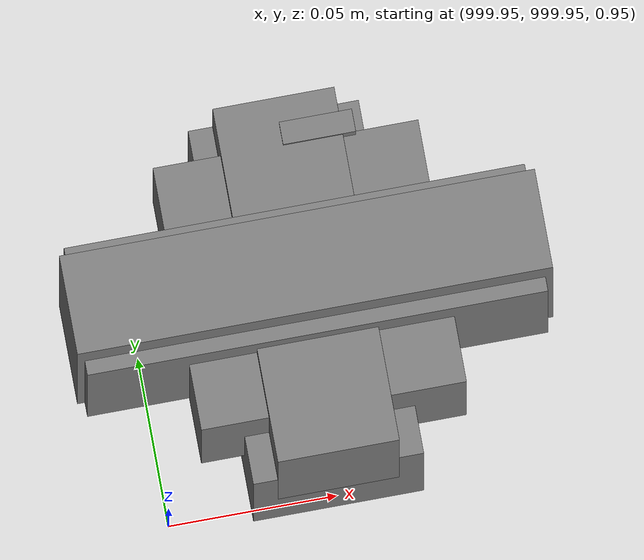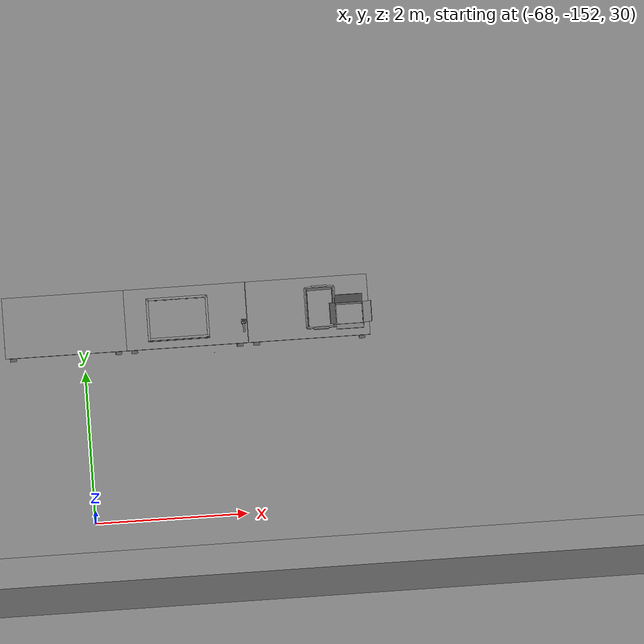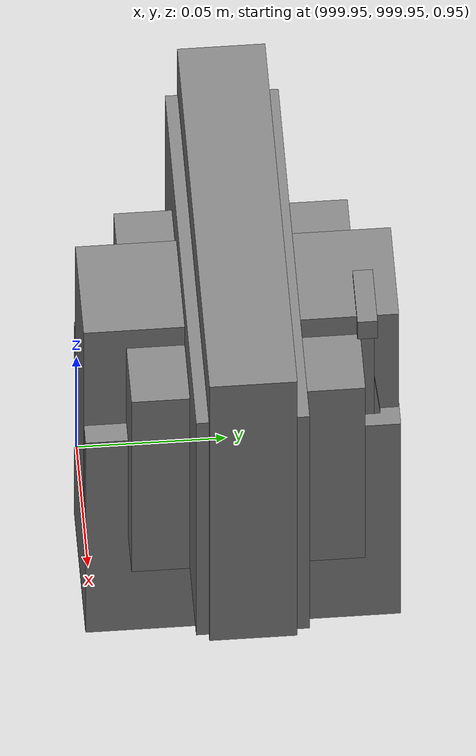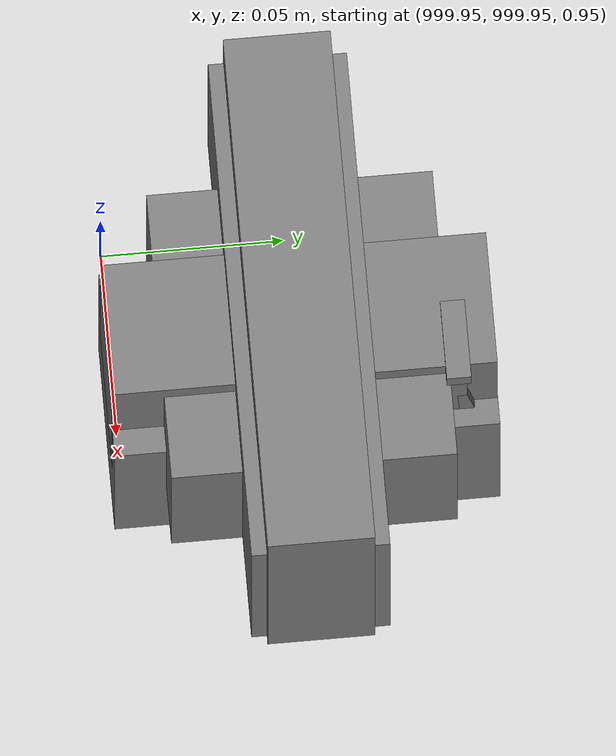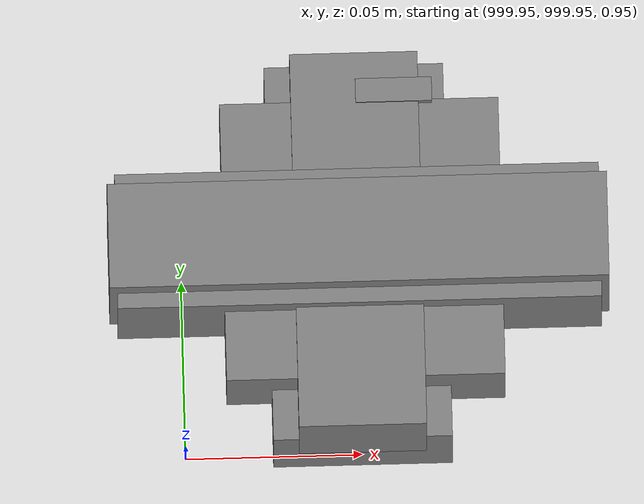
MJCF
<mujoco>
    <option gravity="0.000000000 0.000000000 -9.810000420" timestep="0.0049999999" integrator="implicitfast" density="1.225" viscosity="1.8000001e-05" noslip_iterations="10" iterations="100" sdf_iterations="50">
        <flag multiccd="disable"/>
    </option>
    <size memory="1000M"/>
    <compiler coordinate="local"/>
    <worldbody>
        <light cutoff="30" pos="0 1 1" dir="0 -1 -2"/>
        <light cutoff="30" pos="0 -1 1" dir="0 1 -2"/>
        <body pos="-64.866622925 -149.383972168 30.183746338" euler="89.999984741 89.999946594 0.000000000" name="openloong_gripper_2f85_fix_base_usda_bluebox_01">
            <geom contype="1" conaffinity="1" density="1000" type="box" material="" rgba="0.500000000 0.500000000 0.500000000 1.000000000" solimp="0.899999976 0.949999988 0.001000000" friction="1.000000000 0.005000000 0.000100000" solref="0.020000000 1.000000000" margin="0" condim="3" group="0" pos="0.276580811 0.187225342 0.000068665" quat="0.707106948 0.000077471 0.707106352 0.000077486" size="0.100000001 0.057999998 0.010000000" name="openloong_gripper_2f85_fix_base_usda_geom_390C70DB_8267_4BB0_A5F1_DD6FEA3F7E4F"/>
            <geom contype="1" conaffinity="1" density="1000" type="box" material="" rgba="0.500000000 0.500000000 0.500000000 1.000000000" solimp="0.899999976 0.949999988 0.001000000" friction="1.000000000 0.005000000 0.000100000" solref="0.020000000 1.000000000" margin="0" condim="3" group="0" pos="0.000000000 0.002883911 0.000000000" quat="0.999999881 0.000000000 0.000000000 0.000000000" size="0.254000008 0.003000000 0.172000006" name="openloong_gripper_2f85_fix_base_usda_geom_86595593_537C_45F3_ABC6_2CF0A7B67402"/>
            <geom contype="1" conaffinity="1" density="1000" type="box" material="" rgba="0.500000000 0.500000000 0.500000000 1.000000000" solimp="0.899999976 0.949999988 0.001000000" friction="1.000000000 0.005000000 0.000100000" solref="0.020000000 1.000000000" margin="0" condim="3" group="0" pos="0.000000000 0.124874115 0.173484802" quat="0.999796331 0.020176515 -0.000000015 0.000000030" size="0.259999990 0.119999997 0.007000000" name="openloong_gripper_2f85_fix_base_usda_geom_681AE9D8_C76C_4CD6_B2BE_6641A578A99D"/>
            <geom contype="1" conaffinity="1" density="1000" type="box" material="" rgba="0.500000000 0.500000000 0.500000000 1.000000000" solimp="0.899999976 0.949999988 0.001000000" friction="1.000000000 0.005000000 0.000100000" solref="0.020000000 1.000000000" margin="0" condim="3" group="0" pos="0.000000000 0.124874115 -0.173469543" quat="0.999796331 -0.020176545 -0.000000015 0.000000000" size="0.259999990 0.119999997 0.007000000" name="openloong_gripper_2f85_fix_base_usda_geom_3D194285_1B0F_4335_81A8_C689F6940668"/>
            <geom contype="1" conaffinity="1" density="1000" type="box" material="" rgba="0.500000000 0.500000000 0.500000000 1.000000000" solimp="0.899999976 0.949999988 0.001000000" friction="1.000000000 0.005000000 0.000100000" solref="0.020000000 1.000000000" margin="0" condim="3" group="0" pos="0.000000000 0.214008331 0.188980103" quat="0.999912977 0.013176724 0.000000015 0.000000000" size="0.259999990 0.029999999 0.012500000" name="openloong_gripper_2f85_fix_base_usda_geom_64CE7819_2585_43AC_A97E_6CE6B7D498DA"/>
            <geom contype="1" conaffinity="1" density="1000" type="box" material="" rgba="0.500000000 0.500000000 0.500000000 1.000000000" solimp="0.899999976 0.949999988 0.001000000" friction="1.000000000 0.005000000 0.000100000" solref="0.020000000 1.000000000" margin="0" condim="3" group="0" pos="-0.258361816 0.125289917 0.001876831" quat="0.702796936 -0.020792112 0.710783124 0.020769298" size="0.189999998 0.119999997 0.009000000" name="openloong_gripper_2f85_fix_base_usda_geom_E4F1B891_90E3_40B7_B87F_9D10ABF123BE"/>
            <geom contype="1" conaffinity="1" density="1000" type="box" material="" rgba="0.500000000 0.500000000 0.500000000 1.000000000" solimp="0.899999976 0.949999988 0.001000000" friction="1.000000000 0.005000000 0.000100000" solref="0.020000000 1.000000000" margin="0" condim="3" group="0" pos="0.000000000 0.214008331 -0.188980103" quat="0.999912977 -0.013176769 0.000000030 0.000000015" size="0.259999990 0.029999999 0.012500000" name="openloong_gripper_2f85_fix_base_usda_geom_27B5F9F4_E15F_4F7B_9391_CC2F3973B234"/>
            <geom contype="1" conaffinity="1" density="1000" type="box" material="" rgba="0.500000000 0.500000000 0.500000000 1.000000000" solimp="0.899999976 0.949999988 0.001000000" friction="1.000000000 0.005000000 0.000100000" solref="0.020000000 1.000000000" margin="0" condim="3" group="0" pos="-0.276611328 0.187225342 0.000068665" quat="0.707106650 0.000077441 0.707106709 0.000077456" size="0.100000001 0.057999998 0.010000000" name="openloong_gripper_2f85_fix_base_usda_geom_FF16B91F_6536_4741_BCF3_18F33332990D"/>
            <geom contype="1" conaffinity="1" density="1000" type="box" material="" rgba="0.500000000 0.500000000 0.500000000 1.000000000" solimp="0.899999976 0.949999988 0.001000000" friction="1.000000000 0.005000000 0.000100000" solref="0.020000000 1.000000000" margin="0" condim="3" group="0" pos="0.258331299 0.125289917 0.001876831" quat="0.702851415 0.018856421 0.710823774 -0.019329369" size="0.189999998 0.119999997 0.009000000" name="openloong_gripper_2f85_fix_base_usda_geom_59CC63E4_D934_4E66_8D26_DD754DCCBE41"/>
            <freejoint name="openloong_gripper_2f85_fix_base_usda_bluebox_01_joint"/>
            <site size="0.005000000 0.005000000 0.005000000" rgba="0.500000000 0.500000000 0.500000000 1.000000000" pos="0.000000000 0.000000000 0.000000000" quat="0.999961913 0.008726534 0.000000000 0.000000000" group="0" type="sphere" name="openloong_gripper_2f85_fix_base_usda_bluebox_01site"/>
        </body>
        <body pos="-64.496299744 -149.491867065 30.235729218" euler="0.000000000 0.000000000 89.999946594" name="openloong_gripper_2f85_fix_base_usda_cardboardbox_01">
            <geom contype="1" conaffinity="1" density="1000" type="box" material="" rgba="0.500000000 0.500000000 0.500000000 1.000000000" solimp="0.899999976 0.949999988 0.001000000" friction="1.000000000 0.005000000 0.000100000" solref="0.020000000 1.000000000" margin="0" condim="3" group="0" pos="-0.003166199 -0.004086494 0.005052090" quat="1.000000000 0.000000000 0.000000000 0.000000000" size="0.142499998 0.177500010 0.005000000" name="openloong_gripper_2f85_fix_base_usda_geom_61D0AFDC_331C_49E1_8083_AFBF17DBCF5C"/>
            <geom contype="1" conaffinity="1" density="1000" type="box" material="" rgba="0.500000000 0.500000000 0.500000000 1.000000000" solimp="0.899999976 0.949999988 0.001000000" friction="1.000000000 0.005000000 0.000100000" solref="0.020000000 1.000000000" margin="0" condim="3" group="0" pos="-0.003166199 0.170316696 0.150570869" quat="1.000000000 0.000000000 0.000000000 0.000000000" size="0.142499998 0.005000000 0.149999991" name="openloong_gripper_2f85_fix_base_usda_geom_303D074C_FB0F_4908_AEF1_B98A8884A4D5"/>
            <geom contype="1" conaffinity="1" density="1000" type="box" material="" rgba="0.500000000 0.500000000 0.500000000 1.000000000" solimp="0.899999976 0.949999988 0.001000000" friction="1.000000000 0.005000000 0.000100000" solref="0.020000000 1.000000000" margin="0" condim="3" group="0" pos="-0.147399902 -0.005307198 0.150570869" quat="1.000000000 0.000000000 0.000000000 0.000000000" size="0.005000000 0.177500010 0.149999991" name="openloong_gripper_2f85_fix_base_usda_geom_01D043A4_D86A_4ABC_9BF8_E51AE5436080"/>
            <geom contype="1" conaffinity="1" density="1000" type="box" material="" rgba="0.500000000 0.500000000 0.500000000 1.000000000" solimp="0.899999976 0.949999988 0.001000000" friction="1.000000000 0.005000000 0.000100000" solref="0.020000000 1.000000000" margin="0" condim="3" group="0" pos="0.140275955 -0.005307198 0.150570869" quat="1.000000000 0.000000000 0.000000000 0.000000000" size="0.005000000 0.177500010 0.149999991" name="openloong_gripper_2f85_fix_base_usda_geom_93672A41_EE4A_4938_9681_FC830301968A"/>
            <geom contype="1" conaffinity="1" density="1000" type="box" material="" rgba="0.500000000 0.500000000 0.500000000 1.000000000" solimp="0.899999976 0.949999988 0.001000000" friction="1.000000000 0.005000000 0.000100000" solref="0.020000000 1.000000000" margin="0" condim="3" group="0" pos="-0.003166199 -0.181550980 0.150570869" quat="1.000000000 0.000000000 0.000000000 0.000000000" size="0.142499998 0.005000000 0.149999991" name="openloong_gripper_2f85_fix_base_usda_geom_1A1D7677_CD13_437F_A2E9_9D99A49906D9"/>
            <freejoint name="openloong_gripper_2f85_fix_base_usda_cardboardbox_01_joint"/>
            <site size="0.005000000 0.005000000 0.005000000" rgba="0.500000000 0.500000000 0.500000000 1.000000000" pos="0.000000000 0.000000000 0.000000000" quat="0.999961913 0.008726535 0.000000000 0.000000000" group="0" type="sphere" name="openloong_gripper_2f85_fix_base_usda_site_163EAB12_8AED_4F3E_9E19_2C375B110F32"/>
            <body pos="0.139160156 -0.004048347 0.301930904" euler="-179.999954224 49.383502960 179.999954224" name="openloong_gripper_2f85_fix_base_usda_A1_006">
                <geom contype="1" conaffinity="1" density="1000" type="box" material="" rgba="0.500000000 0.500000000 0.500000000 1.000000000" solimp="0.899999976 0.949999988 0.001000000" friction="1.000000000 0.005000000 0.000100000" solref="0.020000000 1.000000000" margin="0" condim="3" group="0" pos="-0.071587563 0.000009537 0.001745224" quat="0.999999881 0.000000000 0.000000000 0.000000000" size="0.071249999 0.179999992 0.002500000" name="openloong_gripper_2f85_fix_base_usda_geom_E1B7DD4E_560A_4D07_A38B_74A1839442B7"/>
                <joint armature="0" stiffness="0.07" damping="0.0099999998" axis="0.000000 1.000000 0.000000" type="hinge" name="openloong_gripper_2f85_fix_base_usda_A1_006"/>
            </body>
            <body pos="-0.145902634 -0.004086494 0.301938057" euler="-180.000000000 -60.000011444 -180.000000000" name="openloong_gripper_2f85_fix_base_usda_A2_006">
                <geom contype="1" conaffinity="1" density="1000" type="box" material="" rgba="0.500000000 0.500000000 0.500000000 1.000000000" solimp="0.899999976 0.949999988 0.001000000" friction="1.000000000 0.005000000 0.000100000" solref="0.020000000 1.000000000" margin="0" condim="3" group="0" pos="0.071268082 0.000009537 0.002717972" quat="0.000002921 0.000000000 -0.000000030 0.999999881" size="0.071249999 0.179999992 0.002500000" name="openloong_gripper_2f85_fix_base_usda_geom_438521AF_C80B_4F3B_9A8D_3675C7F88400"/>
                <joint armature="0" stiffness="0.07" damping="0.0099999998" axis="0.000000 1.000000 0.000000" type="hinge" name="openloong_gripper_2f85_fix_base_usda_A2_006"/>
            </body>
            <body pos="-0.003385544 0.175991058 0.301930904" euler="-125.858116150 -0.000004561 0.000002331" name="openloong_gripper_2f85_fix_base_usda_B2_006">
                <geom contype="1" conaffinity="1" density="1000" type="box" material="" rgba="0.500000000 0.500000000 0.500000000 1.000000000" solimp="0.899999976 0.949999988 0.001000000" friction="1.000000000 0.005000000 0.000100000" solref="0.020000000 1.000000000" margin="0" condim="3" group="0" pos="0.000009537 -0.070939064 -0.002470016" quat="0.999614120 0.027776197 -0.000000015 0.000000030" size="0.137500003 0.064999998 0.005000000" name="openloong_gripper_2f85_fix_base_usda_geom_79C15D40_A6F2_4172_88A3_FE7FD1EB6AE7"/>
                <joint armature="0" stiffness="0.07" damping="0.0099999998" axis="1.000000 0.000000 0.000000" type="hinge" name="openloong_gripper_2f85_fix_base_usda_B2_006"/>
            </body>
            <body pos="-0.003385544 -0.184140205 0.301938057" euler="147.805557251 0.000000000 0.000000000" name="openloong_gripper_2f85_fix_base_usda_B1_006">
                <geom contype="1" conaffinity="1" density="1000" type="box" material="" rgba="0.500000000 0.500000000 0.500000000 1.000000000" solimp="0.899999976 0.949999988 0.001000000" friction="1.000000000 0.005000000 0.000100000" solref="0.020000000 1.000000000" margin="0" condim="3" group="0" pos="-0.000028610 0.070202351 -0.002703667" quat="0.999614179 -0.027776167 0.000000000 0.000000000" size="0.137500003 0.064999998 0.005000000" name="openloong_gripper_2f85_fix_base_usda_geom_96F2117E_C4A3_4298_A36A_F0FAB320B36D"/>
                <joint armature="0" stiffness="0.07" damping="0.0099999998" axis="1.000000 0.000000 0.000000" type="hinge" name="openloong_gripper_2f85_fix_base_usda_B1_006"/>
            </body>
        </body>
        <body pos="-65.882858276 -149.481979370 30.229999542" euler="-64.487716675 0.000000000 0.000000000" name="openloong_gripper_2f85_fix_base_usda_Barcode">
            <geom contype="1" conaffinity="1" density="1000" type="box" material="" rgba="0.500000000 0.500000000 0.500000000 1.000000000" solimp="0.899999976 0.949999988 0.001000000" friction="1.000000000 0.005000000 0.000100000" solref="0.020000000 1.000000000" margin="0" condim="3" group="0" pos="0.000000000 0.013038635 0.001419067" quat="0.000000000 0.000000000 0.000000000 1.000000119" size="0.034000002 0.010000000 0.017999999" name="openloong_gripper_2f85_fix_base_usda_geom_85F3271B_D8A2_48C4_B801_77915E1BFBF4"/>
            <geom contype="1" conaffinity="1" density="1000" type="box" material="" rgba="0.500000000 0.500000000 0.500000000 1.000000000" solimp="0.899999976 0.949999988 0.001000000" friction="1.000000000 0.005000000 0.000100000" solref="0.020000000 1.000000000" margin="0" condim="3" group="0" pos="0.000000000 -0.035301208 -0.007095337" quat="0.000000000 0.000000000 -0.043619365 0.999048233" size="0.028999999 0.010000000 0.020000000" name="openloong_gripper_2f85_fix_base_usda_geom_CC573C09_DE38_4C4B_88E8_CFE1C3D9D17C"/>
            <geom contype="1" conaffinity="1" density="1000" type="box" material="" rgba="0.500000000 0.500000000 0.500000000 1.000000000" solimp="0.899999976 0.949999988 0.001000000" friction="1.000000000 0.005000000 0.000100000" solref="0.020000000 1.000000000" margin="0" condim="3" group="0" pos="0.000000000 -0.043411255 -0.011749268" quat="0.922262907 0.386563420 0.000000000 0.000000000" size="0.026000001 0.010000000 0.020000000" name="openloong_gripper_2f85_fix_base_usda_geom_1013D5AF_9148_423E_A304_1CF747C2C5E8"/>
            <geom contype="1" conaffinity="1" density="1000" type="box" material="" rgba="0.500000000 0.500000000 0.500000000 1.000000000" solimp="0.899999976 0.949999988 0.001000000" friction="1.000000000 0.005000000 0.000100000" solref="0.020000000 1.000000000" margin="0" condim="3" group="0" pos="0.000000000 -0.016967773 -0.031860352" quat="0.000000000 0.000000000 0.000000000 1.000000119" size="0.008000000 0.010000000 0.013000000" name="openloong_gripper_2f85_fix_base_usda_geom_729F2F12_77CE_4BAF_B5BE_11CA58A68BF9"/>
            <geom contype="1" conaffinity="1" density="1000" type="box" material="" rgba="0.500000000 0.500000000 0.500000000 1.000000000" solimp="0.899999976 0.949999988 0.001000000" friction="1.000000000 0.005000000 0.000100000" solref="0.020000000 1.000000000" margin="0" condim="3" group="0" pos="0.000000000 -0.001869202 0.000312805" quat="0.953716993 0.300705761 0.000000000 0.000000000" size="0.032000002 0.010000000 0.018999999" name="openloong_gripper_2f85_fix_base_usda_geom_01E64FC4_E533_4AD6_9671_3C6B3D7B1061"/>
            <geom contype="1" conaffinity="1" density="1000" type="box" material="" rgba="0.500000000 0.500000000 0.500000000 1.000000000" solimp="0.899999976 0.949999988 0.001000000" friction="1.000000000 0.005000000 0.000100000" solref="0.020000000 1.000000000" margin="0" condim="3" group="0" pos="0.000000000 -0.019531250 -0.003173828" quat="0.953716993 0.300705761 0.000000000 0.000000000" size="0.030999999 0.010000000 0.020000000" name="openloong_gripper_2f85_fix_base_usda_geom_0A4BEA62_0AE9_4EEE_A16E_1B4EBD15FC88"/>
            <geom contype="1" conaffinity="1" density="1000" type="box" material="" rgba="0.500000000 0.500000000 0.500000000 1.000000000" solimp="0.899999976 0.949999988 0.001000000" friction="1.000000000 0.005000000 0.000100000" solref="0.020000000 1.000000000" margin="0" condim="3" group="0" pos="0.000000000 -0.035301208 -0.007095337" quat="0.953716993 0.300705761 0.000000000 0.000000000" size="0.028999999 0.010000000 0.020000000" name="openloong_gripper_2f85_fix_base_usda_geom_3B1B1E86_A85B_4316_A834_EA143ED3B8A7"/>
            <geom contype="1" conaffinity="1" density="1000" type="box" material="" rgba="0.500000000 0.500000000 0.500000000 1.000000000" solimp="0.899999976 0.949999988 0.001000000" friction="1.000000000 0.005000000 0.000100000" solref="0.020000000 1.000000000" margin="0" condim="3" group="0" pos="0.000000000 -0.042617798 -0.071121216" quat="0.000000000 0.000000000 0.000000000 1.000000119" size="0.013000000 0.021000000 0.059999999" name="openloong_gripper_2f85_fix_base_usda_geom_8E83D4F7_73A3_4C7C_9B22_7514CAFA14B0"/>
            <freejoint name="openloong_gripper_2f85_fix_base_usda_Barcode_joint"/>
            <site size="0.005000000 0.005000000 0.005000000" rgba="0.500000000 0.500000000 0.500000000 1.000000000" pos="0.000000000 0.000000000 0.000000000" quat="1.000000000 0.000000000 0.000000000 0.000000000" group="0" type="sphere" name="openloong_gripper_2f85_fix_base_usda_Barcode_site"/>
        </body>
        <body pos="-66.745018005 -149.392349243 30.184000015" euler="0.000000000 0.000000000 89.999946594" name="[22330042560393]_Basket_01">
            <geom contype="1" conaffinity="1" density="1000" type="box" material="" rgba="0.500000000 0.500000000 0.500000000 1.000000000" solimp="0.899999976 0.949999988 0.001000000" friction="1.000000000 0.005000000 0.000100000" solref="0.020000000 1.000000000" margin="0" condim="3" group="0" pos="-0.052425385 0.389207840 0.089787483" quat="0.707107008 0.000000000 0.000000000 0.707106411" size="0.014249999 0.014249999 0.059999999" name="[22330042560393]_geom_19E1E4A1_BDC9_4819_9BE3_B55B993D65E1"/>
            <geom contype="1" conaffinity="1" density="1000" type="box" material="" rgba="0.500000000 0.500000000 0.500000000 1.000000000" solimp="0.899999976 0.949999988 0.001000000" friction="1.000000000 0.005000000 0.000100000" solref="0.020000000 1.000000000" margin="0" condim="3" group="0" pos="0.264015198 -0.133043289 0.089787483" quat="0.707107008 0.000000000 0.000000000 0.707106411" size="0.014249999 0.014249999 0.059999999" name="[22330042560393]_geom_E2035491_2606_42ED_9509_D7953003431D"/>
            <geom contype="1" conaffinity="1" density="1000" type="box" material="" rgba="0.500000000 0.500000000 0.500000000 1.000000000" solimp="0.899999976 0.949999988 0.001000000" friction="1.000000000 0.005000000 0.000100000" solref="0.020000000 1.000000000" margin="0" condim="3" group="0" pos="-0.264015198 -0.265548706 0.089793205" quat="0.707107008 0.000000000 0.000000000 0.707106411" size="0.014249999 0.014249999 0.059999999" name="[22330042560393]_geom_365DE4A8_3D59_4F9F_B090_B9FA12AD6C5C"/>
            <geom contype="1" conaffinity="1" density="1000" type="box" material="" rgba="0.500000000 0.500000000 0.500000000 1.000000000" solimp="0.899999976 0.949999988 0.001000000" friction="1.000000000 0.005000000 0.000100000" solref="0.020000000 1.000000000" margin="0" condim="3" group="0" pos="-0.160263062 -0.389322281 0.089793205" quat="0.707107008 0.000000000 0.000000000 0.707106411" size="0.014249999 0.014249999 0.059999999" name="[22330042560393]_geom_498DA423_1CD2_4749_B5AC_E313E6517BA0"/>
            <geom contype="1" conaffinity="1" density="1000" type="box" material="" rgba="0.500000000 0.500000000 0.500000000 1.000000000" solimp="0.899999976 0.949999988 0.001000000" friction="1.000000000 0.005000000 0.000100000" solref="0.020000000 1.000000000" margin="0" condim="3" group="0" pos="0.162265778 -0.389322281 0.089787483" quat="0.707107008 0.000000000 0.000000000 0.707106411" size="0.014249999 0.014249999 0.059999999" name="[22330042560393]_geom_C8235CEC_890E_4C3B_82F6_242FB511BB63"/>
            <geom contype="1" conaffinity="1" density="1000" type="box" material="" rgba="0.500000000 0.500000000 0.500000000 1.000000000" solimp="0.899999976 0.949999988 0.001000000" friction="1.000000000 0.005000000 0.000100000" solref="0.020000000 1.000000000" margin="0" condim="3" group="0" pos="0.264015198 0.389207840 0.089787483" quat="0.707107008 0.000000000 0.000000000 0.707106411" size="0.014249999 0.014249999 0.059999999" name="[22330042560393]_geom_53CC37F2_7069_4721_97BB_A40FEB33604A"/>
            <geom contype="1" conaffinity="1" density="1000" type="box" material="" rgba="0.500000000 0.500000000 0.500000000 1.000000000" solimp="0.899999976 0.949999988 0.001000000" friction="1.000000000 0.005000000 0.000100000" solref="0.020000000 1.000000000" margin="0" condim="3" group="0" pos="-0.264015198 -0.133043289 0.089793205" quat="0.707107008 0.000000000 0.000000000 0.707106411" size="0.014249999 0.014249999 0.059999999" name="[22330042560393]_geom_C5558CAB_8FDD_4F7B_8CB4_558C398F6770"/>
            <geom contype="1" conaffinity="1" density="1000" type="box" material="" rgba="0.500000000 0.500000000 0.500000000 1.000000000" solimp="0.899999976 0.949999988 0.001000000" friction="1.000000000 0.005000000 0.000100000" solref="0.020000000 1.000000000" margin="0" condim="3" group="0" pos="-0.264026642 0.269256592 0.089793205" quat="0.707107008 0.000000000 0.000000000 0.707106411" size="0.014249999 0.014249999 0.059999999" name="[22330042560393]_geom_C6C0A3F3_DB26_4CD9_B633_FC640FAAB5EC"/>
            <geom contype="1" conaffinity="1" density="1000" type="box" material="" rgba="0.500000000 0.500000000 0.500000000 1.000000000" solimp="0.899999976 0.949999988 0.001000000" friction="1.000000000 0.005000000 0.000100000" solref="0.020000000 1.000000000" margin="0" condim="3" group="0" pos="0.054462433 0.389207840 0.089787483" quat="0.707107008 0.000000000 0.000000000 0.707106411" size="0.014249999 0.014249999 0.059999999" name="[22330042560393]_geom_6C5ACDEB_F4D8_4E75_B330_A76120697BBF"/>
            <geom contype="1" conaffinity="1" density="1000" type="box" material="" rgba="0.500000000 0.500000000 0.500000000 1.000000000" solimp="0.899999976 0.949999988 0.001000000" friction="1.000000000 0.005000000 0.000100000" solref="0.020000000 1.000000000" margin="0" condim="3" group="0" pos="0.054462433 -0.389322281 0.089787483" quat="0.707107008 0.000000000 0.000000000 0.707106411" size="0.014249999 0.014249999 0.059999999" name="[22330042560393]_geom_6D537111_00ED_493D_B406_1B34EAF84EE4"/>
            <geom contype="1" conaffinity="1" density="1000" type="box" material="" rgba="0.500000000 0.500000000 0.500000000 1.000000000" solimp="0.899999976 0.949999988 0.001000000" friction="1.000000000 0.005000000 0.000100000" solref="0.020000000 1.000000000" margin="0" condim="3" group="0" pos="0.264015198 0.269256592 0.089793205" quat="0.707107008 0.000000000 0.000000000 0.707106411" size="0.014249999 0.014249999 0.059999999" name="[22330042560393]_geom_CA0D136B_2627_4815_8C72_A3741F3DF018"/>
            <geom contype="1" conaffinity="1" density="1000" type="box" material="" rgba="0.500000000 0.500000000 0.500000000 1.000000000" solimp="0.899999976 0.949999988 0.001000000" friction="1.000000000 0.005000000 0.000100000" solref="0.020000000 1.000000000" margin="0" condim="3" group="0" pos="0.264015198 -0.389322281 0.089787483" quat="0.707107008 0.000000000 0.000000000 0.707106411" size="0.014249999 0.014249999 0.059999999" name="[22330042560393]_geom_6D430D7A_2A7D_4F29_9C2E_F56F8E6C36E2"/>
            <geom contype="1" conaffinity="1" density="1000" type="box" material="" rgba="0.500000000 0.500000000 0.500000000 1.000000000" solimp="0.899999976 0.949999988 0.001000000" friction="1.000000000 0.005000000 0.000100000" solref="0.020000000 1.000000000" margin="0" condim="3" group="0" pos="0.000000000 0.000000000 0.015998840" quat="0.707107008 0.000000000 0.000000000 0.707106411" size="0.403499991 0.279000014 0.015750000" name="[22330042560393]_geom_00F7B10A_DB45_47CE_85E1_50786D61FCAD"/>
            <geom contype="1" conaffinity="1" density="1000" type="box" material="" rgba="0.500000000 0.500000000 0.500000000 1.000000000" solimp="0.899999976 0.949999988 0.001000000" friction="1.000000000 0.005000000 0.000100000" solref="0.020000000 1.000000000" margin="0" condim="3" group="0" pos="0.000000000 -0.389476776 0.163619041" quat="0.707107008 0.000000000 0.000000000 0.707106411" size="0.015000000 0.277500004 0.015750000" name="[22330042560393]_geom_BD65EC3F_EF29_4B5D_8640_C7039903112B"/>
            <geom contype="1" conaffinity="1" density="1000" type="box" material="" rgba="0.500000000 0.500000000 0.500000000 1.000000000" solimp="0.899999976 0.949999988 0.001000000" friction="1.000000000 0.005000000 0.000100000" solref="0.020000000 1.000000000" margin="0" condim="3" group="0" pos="0.162265778 0.389207840 0.089787483" quat="0.707107008 0.000000000 0.000000000 0.707106411" size="0.014249999 0.014249999 0.059999999" name="[22330042560393]_geom_15FB601B_24E5_47AD_933E_0B7F78C9E46D"/>
            <geom contype="1" conaffinity="1" density="1000" type="box" material="" rgba="0.500000000 0.500000000 0.500000000 1.000000000" solimp="0.899999976 0.949999988 0.001000000" friction="1.000000000 0.005000000 0.000100000" solref="0.020000000 1.000000000" margin="0" condim="3" group="0" pos="0.000000000 0.389471054 0.163619041" quat="0.707107008 0.000000000 0.000000000 0.707106411" size="0.015000000 0.277500004 0.015750000" name="[22330042560393]_geom_CCD05E0C_C21F_435E_A49C_D40E30DCCA69"/>
            <geom contype="1" conaffinity="1" density="1000" type="box" material="" rgba="0.500000000 0.500000000 0.500000000 1.000000000" solimp="0.899999976 0.949999988 0.001000000" friction="1.000000000 0.005000000 0.000100000" solref="0.020000000 1.000000000" margin="0" condim="3" group="0" pos="-0.263511658 0.000000000 0.163619041" quat="0.707107008 0.000000000 0.000000000 0.707106411" size="0.403499991 0.015000000 0.015750000" name="[22330042560393]_geom_40270999_099D_4E4D_9DE6_A58877FCC977"/>
            <geom contype="1" conaffinity="1" density="1000" type="box" material="" rgba="0.500000000 0.500000000 0.500000000 1.000000000" solimp="0.899999976 0.949999988 0.001000000" friction="1.000000000 0.005000000 0.000100000" solref="0.020000000 1.000000000" margin="0" condim="3" group="0" pos="-0.264015198 0.141334534 0.089793205" quat="0.707107008 0.000000000 0.000000000 0.707106411" size="0.014249999 0.014249999 0.059999999" name="[22330042560393]_geom_78C8BF20_78E5_42FA_BC88_C6A1780C4868"/>
            <geom contype="1" conaffinity="1" density="1000" type="box" material="" rgba="0.500000000 0.500000000 0.500000000 1.000000000" solimp="0.899999976 0.949999988 0.001000000" friction="1.000000000 0.005000000 0.000100000" solref="0.020000000 1.000000000" margin="0" condim="3" group="0" pos="0.264015198 -0.265548706 0.089787483" quat="0.707107008 0.000000000 0.000000000 0.707106411" size="0.014249999 0.014249999 0.059999999" name="[22330042560393]_geom_DF070678_0A97_4EE1_959A_03137105FB4E"/>
            <geom contype="1" conaffinity="1" density="1000" type="box" material="" rgba="0.500000000 0.500000000 0.500000000 1.000000000" solimp="0.899999976 0.949999988 0.001000000" friction="1.000000000 0.005000000 0.000100000" solref="0.020000000 1.000000000" margin="0" condim="3" group="0" pos="-0.160263062 0.389207840 0.089787483" quat="0.707107008 0.000000000 0.000000000 0.707106411" size="0.014249999 0.014249999 0.059999999" name="[22330042560393]_geom_9AA176B7_541B_4EE2_B275_BBC0A120B2F1"/>
            <geom contype="1" conaffinity="1" density="1000" type="box" material="" rgba="0.500000000 0.500000000 0.500000000 1.000000000" solimp="0.899999976 0.949999988 0.001000000" friction="1.000000000 0.005000000 0.000100000" solref="0.020000000 1.000000000" margin="0" condim="3" group="0" pos="-0.052425385 -0.389322281 0.089787483" quat="0.707107008 0.000000000 0.000000000 0.707106411" size="0.014249999 0.014249999 0.059999999" name="[22330042560393]_geom_B7ABA695_FE45_4652_904D_2379DBC9B9EF"/>
            <geom contype="1" conaffinity="1" density="1000" type="box" material="" rgba="0.500000000 0.500000000 0.500000000 1.000000000" solimp="0.899999976 0.949999988 0.001000000" friction="1.000000000 0.005000000 0.000100000" solref="0.020000000 1.000000000" margin="0" condim="3" group="0" pos="-0.264026642 -0.389322281 0.089793205" quat="0.707107008 0.000000000 0.000000000 0.707106411" size="0.014249999 0.014249999 0.059999999" name="[22330042560393]_geom_8C098F33_25FA_4E15_B6BC_A961E86976EF"/>
            <geom contype="1" conaffinity="1" density="1000" type="box" material="" rgba="0.500000000 0.500000000 0.500000000 1.000000000" solimp="0.899999976 0.949999988 0.001000000" friction="1.000000000 0.005000000 0.000100000" solref="0.020000000 1.000000000" margin="0" condim="3" group="0" pos="0.264015198 0.141334534 0.089787483" quat="0.707107008 0.000000000 0.000000000 0.707106411" size="0.014249999 0.014249999 0.059999999" name="[22330042560393]_geom_F12C5635_124D_465B_A91B_62150C74995A"/>
            <geom contype="1" conaffinity="1" density="1000" type="box" material="" rgba="0.500000000 0.500000000 0.500000000 1.000000000" solimp="0.899999976 0.949999988 0.001000000" friction="1.000000000 0.005000000 0.000100000" solref="0.020000000 1.000000000" margin="0" condim="3" group="0" pos="-0.264015198 0.389207840 0.089793205" quat="0.707107008 0.000000000 0.000000000 0.707106411" size="0.014249999 0.014249999 0.059999999" name="[22330042560393]_geom_4AAC5432_48F4_42B1_B46B_16B2EB567649"/>
            <geom contype="1" conaffinity="1" density="1000" type="box" material="" rgba="0.500000000 0.500000000 0.500000000 1.000000000" solimp="0.899999976 0.949999988 0.001000000" friction="1.000000000 0.005000000 0.000100000" solref="0.020000000 1.000000000" margin="0" condim="3" group="0" pos="0.264015198 0.004480362 0.089787483" quat="0.707107008 0.000000000 0.000000000 0.707106411" size="0.014249999 0.014249999 0.059999999" name="[22330042560393]_geom_13CD04F2_35BB_4F15_AF96_5F0715B52362"/>
            <geom contype="1" conaffinity="1" density="1000" type="box" material="" rgba="0.500000000 0.500000000 0.500000000 1.000000000" solimp="0.899999976 0.949999988 0.001000000" friction="1.000000000 0.005000000 0.000100000" solref="0.020000000 1.000000000" margin="0" condim="3" group="0" pos="0.263694763 -0.000011444 0.163619041" quat="0.707107008 0.000000000 0.000000000 0.707106411" size="0.403499991 0.015000000 0.015750000" name="[22330042560393]_geom_8F277210_347B_49CB_BDCA_A50707F4BAB5"/>
            <geom contype="1" conaffinity="1" density="1000" type="box" material="" rgba="0.500000000 0.500000000 0.500000000 1.000000000" solimp="0.899999976 0.949999988 0.001000000" friction="1.000000000 0.005000000 0.000100000" solref="0.020000000 1.000000000" margin="0" condim="3" group="0" pos="-0.264015198 0.004480362 0.089793205" quat="0.707107008 0.000000000 0.000000000 0.707106411" size="0.014249999 0.014249999 0.059999999" name="[22330042560393]_geom_04AF42D5_0B92_4A58_A04C_A999D0330DC5"/>
            <freejoint name="[22330042560393]_joint_55387C36_E422_4850_ABED_19F0C2F5D637"/>
        </body>
        <body pos="0.000000000 0.000000000 0.000000000" euler="0.000000000 0.000000000 0.000000000" name="Static Objects_Static Objects">
            <geom contype="1" conaffinity="1" density="1000" type="box" material="" rgba="0.500000000 0.500000000 0.500000000 1.000000000" solimp="0.899999976 0.949999988 0.001000000" friction="1.000000000 0.005000000 0.000100000" solref="0.020000000 1.000000000" margin="0" condim="3" group="0" pos="-67.544113159 -149.365814209 29.727830887" quat="0.500000417 0.499999970 0.499999553 0.499999970" size="0.381000012 0.319999993 0.041000001" name="Static Objects_geom_C8692E24_38D1_47CA_ACB1_1D4262B09029"/>
            <geom contype="1" conaffinity="1" density="1000" type="box" material="" rgba="0.500000000 0.500000000 0.500000000 1.000000000" solimp="0.899999976 0.949999988 0.001000000" friction="1.000000000 0.005000000 0.000100000" solref="0.020000000 1.000000000" margin="0" condim="3" group="0" pos="-68.239501953 -149.365814209 30.086868286" quat="0.500000417 0.499999970 0.499999553 0.499999970" size="0.370999992 0.039500002 0.745000005" name="Static Objects_geom_92310464_439D_4C0F_85D9_8CFB4A5B5FDC"/>
            <geom contype="1" conaffinity="1" density="1000" type="box" material="" rgba="0.500000000 0.500000000 0.500000000 1.000000000" solimp="0.899999976 0.949999988 0.001000000" friction="1.000000000 0.005000000 0.000100000" solref="0.020000000 1.000000000" margin="0" condim="3" group="0" pos="-68.239501953 -149.365814209 30.147235870" quat="0.500000417 0.499999970 0.499999553 0.499999970" size="0.400000006 0.022000000 0.800000012" name="Static Objects_geom_333EDE7F_99E9_490F_9C08_D39B94D4337F"/>
            <geom contype="1" conaffinity="1" density="1000" type="box" material="" rgba="0.500000000 0.500000000 0.500000000 1.000000000" solimp="0.899999976 0.949999988 0.001000000" friction="1.000000000 0.005000000 0.000100000" solref="0.020000000 1.000000000" margin="0" condim="3" group="0" pos="-68.934890747 -149.365814209 29.727830887" quat="0.500000417 0.499999970 0.499999553 0.499999970" size="0.381000012 0.319999993 0.041000001" name="Static Objects_geom_51C0A5D4_EBEE_435D_B51D_F214B267BAA3"/>
            <geom contype="1" conaffinity="1" density="1000" type="box" material="" rgba="0.500000000 0.500000000 0.500000000 1.000000000" solimp="0.899999976 0.949999988 0.001000000" friction="1.000000000 0.005000000 0.000100000" solref="0.020000000 1.000000000" margin="0" condim="3" group="0" pos="-68.239501953 -149.365814209 29.561563492" quat="0.500000417 0.499999970 0.499999553 0.499999970" size="0.020000000 0.022000000 0.660000026" name="Static Objects_geom_FC514F2E_5674_4E64_A066_AEF40E998DC3"/>
            <geom contype="1" conaffinity="1" density="1000" type="box" material="" rgba="0.500000000 0.500000000 0.500000000 1.000000000" solimp="0.899999976 0.949999988 0.001000000" friction="1.000000000 0.005000000 0.000100000" solref="0.020000000 1.000000000" margin="0" condim="3" group="0" pos="-65.945671082 -149.365814209 29.727830887" quat="0.500000417 0.499999970 0.499999553 0.499999970" size="0.381000012 0.319999993 0.041000001" name="Static Objects_geom_F760EC1D_7000_447D_A7FF_D48D6375F330"/>
            <geom contype="1" conaffinity="1" density="1000" type="box" material="" rgba="0.500000000 0.500000000 0.500000000 1.000000000" solimp="0.899999976 0.949999988 0.001000000" friction="1.000000000 0.005000000 0.000100000" solref="0.020000000 1.000000000" margin="0" condim="3" group="0" pos="-66.641059875 -149.365814209 30.086868286" quat="0.500000417 0.499999970 0.499999553 0.499999970" size="0.370999992 0.039500002 0.745000005" name="Static Objects_geom_81500501_78A5_4609_BCD2_E4980164623F"/>
            <geom contype="1" conaffinity="1" density="1000" type="box" material="" rgba="0.500000000 0.500000000 0.500000000 1.000000000" solimp="0.899999976 0.949999988 0.001000000" friction="1.000000000 0.005000000 0.000100000" solref="0.020000000 1.000000000" margin="0" condim="3" group="0" pos="-66.641059875 -149.365814209 30.147235870" quat="0.500000417 0.499999970 0.499999553 0.499999970" size="0.400000006 0.022000000 0.800000012" name="Static Objects_geom_44CC709F_EF6D_4C5F_96F7_43944CEA3A1F"/>
            <geom contype="1" conaffinity="1" density="1000" type="box" material="" rgba="0.500000000 0.500000000 0.500000000 1.000000000" solimp="0.899999976 0.949999988 0.001000000" friction="1.000000000 0.005000000 0.000100000" solref="0.020000000 1.000000000" margin="0" condim="3" group="0" pos="-67.336448669 -149.365814209 29.727830887" quat="0.500000417 0.499999970 0.499999553 0.499999970" size="0.381000012 0.319999993 0.041000001" name="Static Objects_geom_5FCEAC13_3101_4DFA_BF24_0BB876879AEC"/>
            <geom contype="1" conaffinity="1" density="1000" type="box" material="" rgba="0.500000000 0.500000000 0.500000000 1.000000000" solimp="0.899999976 0.949999988 0.001000000" friction="1.000000000 0.005000000 0.000100000" solref="0.020000000 1.000000000" margin="0" condim="3" group="0" pos="-66.641059875 -149.365814209 29.561563492" quat="0.500000417 0.499999970 0.499999553 0.499999970" size="0.020000000 0.022000000 0.660000026" name="Static Objects_geom_7A31F18A_68FF_498B_BF2D_698C5417E62B"/>
            <geom contype="1" conaffinity="1" density="1000" type="box" material="" rgba="0.500000000 0.500000000 0.500000000 1.000000000" solimp="0.899999976 0.949999988 0.001000000" friction="1.000000000 0.005000000 0.000100000" solref="0.020000000 1.000000000" margin="0" condim="3" group="0" pos="-64.338577271 -149.365814209 29.727830887" quat="0.500000417 0.499999970 0.499999553 0.499999970" size="0.381000012 0.319999993 0.041000001" name="Static Objects_geom_E67123BF_E704_4A00_8AD2_13C7DCC0463D"/>
            <geom contype="1" conaffinity="1" density="1000" type="box" material="" rgba="0.500000000 0.500000000 0.500000000 1.000000000" solimp="0.899999976 0.949999988 0.001000000" friction="1.000000000 0.005000000 0.000100000" solref="0.020000000 1.000000000" margin="0" condim="3" group="0" pos="-65.033966064 -149.365814209 30.086868286" quat="0.500000417 0.499999970 0.499999553 0.499999970" size="0.370999992 0.039500002 0.745000005" name="Static Objects_geom_4DFD21CC_D254_4651_B4F3_75B8E73F9A79"/>
            <geom contype="1" conaffinity="1" density="1000" type="box" material="" rgba="0.500000000 0.500000000 0.500000000 1.000000000" solimp="0.899999976 0.949999988 0.001000000" friction="1.000000000 0.005000000 0.000100000" solref="0.020000000 1.000000000" margin="0" condim="3" group="0" pos="-65.033966064 -149.365814209 30.147235870" quat="0.500000417 0.499999970 0.499999553 0.499999970" size="0.400000006 0.022000000 0.800000012" name="Static Objects_geom_B17964DC_2F50_4938_8AC6_BA893E8B9702"/>
            <geom contype="1" conaffinity="1" density="1000" type="box" material="" rgba="0.500000000 0.500000000 0.500000000 1.000000000" solimp="0.899999976 0.949999988 0.001000000" friction="1.000000000 0.005000000 0.000100000" solref="0.020000000 1.000000000" margin="0" condim="3" group="0" pos="-65.729354858 -149.365814209 29.727830887" quat="0.500000417 0.499999970 0.499999553 0.499999970" size="0.381000012 0.319999993 0.041000001" name="Static Objects_geom_1696C3AD_3F74_4D80_B7B1_1BA1C32EEBDE"/>
            <geom contype="1" conaffinity="1" density="1000" type="box" material="" rgba="0.500000000 0.500000000 0.500000000 1.000000000" solimp="0.899999976 0.949999988 0.001000000" friction="1.000000000 0.005000000 0.000100000" solref="0.020000000 1.000000000" margin="0" condim="3" group="0" pos="-65.033966064 -149.365814209 29.561563492" quat="0.500000417 0.499999970 0.499999553 0.499999970" size="0.020000000 0.022000000 0.660000026" name="Static Objects_geom_9BAE534B_2880_4BCC_A63F_E5AFA905861C"/>
            <geom contype="1" conaffinity="1" density="1000" type="box" material="" rgba="0.500000000 0.500000000 0.500000000 1.000000000" solimp="0.899999976 0.949999988 0.001000000" friction="1.000000000 0.005000000 0.000100000" solref="0.020000000 1.000000000" margin="0" condim="3" group="0" pos="-61.754566193 -137.853729248 33.906845093" quat="0.707107067 0.000000000 0.000000000 0.707106471" size="0.759999990 0.759999990 4.500000000" name="Static Objects_geom_81C4F654_0C13_4E91_A3D3_B22453F174C1"/>
            <geom contype="1" conaffinity="1" density="1000" type="box" material="" rgba="0.500000000 0.500000000 0.500000000 1.000000000" solimp="0.899999976 0.949999988 0.001000000" friction="1.000000000 0.005000000 0.000100000" solref="0.020000000 1.000000000" margin="0" condim="3" group="0" pos="-57.511135101 -144.927108765 31.707921982" quat="1.000000000 0.000000000 0.000000000 0.000000000" size="0.200000003 8.000000000 2.299999952" name="Static Objects_geom_F3FD7D89_DF9F_4E82_BCCC_70D5017878F8"/>
            <geom contype="1" conaffinity="1" density="1000" type="box" material="" rgba="0.500000000 0.500000000 0.500000000 1.000000000" solimp="0.899999976 0.949999988 0.001000000" friction="1.000000000 0.005000000 0.000100000" solref="0.020000000 1.000000000" margin="0" condim="3" group="0" pos="-80.517646790 -157.574050903 31.688196182" quat="0.707107067 0.000000000 0.000000000 0.707106471" size="0.600000024 0.600000024 2.299999952" name="Static Objects_geom_AAA62AF9_94C4_4763_ACF2_2249D680C776"/>
            <geom contype="1" conaffinity="1" density="1000" type="box" material="" rgba="0.500000000 0.500000000 0.500000000 1.000000000" solimp="0.899999976 0.949999988 0.001000000" friction="1.000000000 0.005000000 0.000100000" solref="0.020000000 1.000000000" margin="0" condim="3" group="0" pos="-80.711044312 -147.414932251 31.666158676" quat="1.000000000 0.000000000 0.000000000 0.000000000" size="0.200000003 10.000000000 2.299999952" name="Static Objects_geom_018E17BA_1B40_49F9_BA28_ACB6E09C8105"/>
            <geom contype="1" conaffinity="1" density="1000" type="box" material="" rgba="0.500000000 0.500000000 0.500000000 1.000000000" solimp="0.899999976 0.949999988 0.001000000" friction="1.000000000 0.005000000 0.000100000" solref="0.020000000 1.000000000" margin="0" condim="3" group="0" pos="-57.687217712 -137.434692383 31.688196182" quat="0.707107067 0.000000000 0.000000000 0.707106471" size="0.600000024 0.600000024 2.299999952" name="Static Objects_geom_F4D7EB59_DD55_427A_8B8D_8C4B38BCE9D3"/>
            <geom contype="1" conaffinity="1" density="1000" type="box" material="" rgba="0.500000000 0.500000000 0.500000000 1.000000000" solimp="0.899999976 0.949999988 0.001000000" friction="1.000000000 0.005000000 0.000100000" solref="0.020000000 1.000000000" margin="0" condim="3" group="0" pos="-69.537033081 -140.263229370 31.714921951" quat="0.707107067 0.000000000 0.000000000 0.707106471" size="0.759999990 4.500000000 2.299999952" name="Static Objects_geom_8A4A2A4D_06C1_42D5_89FA_F4953BD89C43"/>
            <geom contype="1" conaffinity="1" density="1000" type="box" material="" rgba="0.500000000 0.500000000 0.500000000 1.000000000" solimp="0.899999976 0.949999988 0.001000000" friction="1.000000000 0.005000000 0.000100000" solref="0.020000000 1.000000000" margin="0" condim="3" group="0" pos="-80.073638916 -137.853713989 33.906845093" quat="0.707107067 0.000000000 0.000000000 0.707106471" size="0.759999990 0.759999990 4.500000000" name="Static Objects_geom_F24C977A_6962_4D1E_98FA_5C72E33EB208"/>
            <geom contype="1" conaffinity="1" density="1000" type="box" material="" rgba="0.500000000 0.500000000 0.500000000 1.000000000" solimp="0.899999976 0.949999988 0.001000000" friction="1.000000000 0.005000000 0.000100000" solref="0.020000000 1.000000000" margin="0" condim="3" group="0" pos="-73.406707764 -155.734664917 31.707921982" quat="1.000000000 0.000000000 0.000000000 0.000000000" size="0.200000003 3.000000000 2.299999952" name="Static Objects_geom_E79750EE_8029_4B5A_BDAA_85478B8C4352"/>
            <geom contype="1" conaffinity="1" density="1000" type="box" material="" rgba="0.500000000 0.500000000 0.500000000 1.000000000" solimp="0.899999976 0.949999988 0.001000000" friction="1.000000000 0.005000000 0.000100000" solref="0.020000000 1.000000000" margin="0" condim="3" group="0" pos="-68.497543335 -137.448257446 31.707921982" quat="0.707107067 0.000000000 0.000000000 0.707106471" size="0.200000003 14.000000000 2.299999952" name="Static Objects_geom_903CAB68_25D5_4C84_AB26_FC8DCE2B1A46"/>
            <geom contype="1" conaffinity="1" density="1000" type="cylinder" material="" rgba="0.500000000 0.500000000 0.500000000 1.000000000" solimp="0.899999976 0.949999988 0.001000000" friction="1.000000000 0.005000000 0.000100000" solref="0.020000000 1.000000000" margin="0" condim="3" group="0" pos="-68.868522644 -142.134506226 31.711090088" quat="0.707107067 0.000000000 0.000000000 0.707106471" size="0.509999990 2.299999952 1.000000000" name="Static Objects_geom_648EE8D3_829C_4130_BF5C_DE780B8F6BCA"/>
            <geom contype="1" conaffinity="1" density="1000" type="plane" material="" rgba="0.500000000 0.500000000 0.500000000 1.000000000" solimp="0.899999976 0.949999988 0.001000000" friction="1.000000000 0.005000000 0.000100000" solref="0.020000000 1.000000000" margin="0" condim="3" group="0" pos="-72.873703003 -147.131927490 29.409669876" quat="1.000000000 0.000000000 0.000000000 0.000000000" size="18.000000000 14.000000000 1.000000000" name="Static Objects_geom_B71BDCE4_22B4_401B_8972_6D928EA5BAAF"/>
            <geom contype="1" conaffinity="1" density="1000" type="box" material="" rgba="0.500000000 0.500000000 0.500000000 1.000000000" solimp="0.899999976 0.949999988 0.001000000" friction="1.000000000 0.005000000 0.000100000" solref="0.020000000 1.000000000" margin="0" condim="3" group="0" pos="-79.943580627 -157.782272339 31.707921982" quat="0.707107067 0.000000000 0.000000000 0.707106471" size="0.200000003 7.000000000 2.299999952" name="Static Objects_geom_3BA384D8_77D1_49A5_B264_422EDBCEB631"/>
            <geom contype="1" conaffinity="1" density="1000" type="box" material="" rgba="0.500000000 0.500000000 0.500000000 1.000000000" solimp="0.899999976 0.949999988 0.001000000" friction="1.000000000 0.005000000 0.000100000" solref="0.020000000 1.000000000" margin="0" condim="3" group="0" pos="-65.421028137 -152.903442383 31.707921982" quat="0.707107067 0.000000000 0.000000000 0.707106471" size="0.200000003 7.800000191 2.299999952" name="Static Objects_geom_4DD256EB_952F_43E7_BEF1_A5DF5D19866C"/>
            <geom contype="1" conaffinity="1" density="1000" type="box" material="" rgba="0.500000000 0.500000000 0.500000000 1.000000000" solimp="0.899999976 0.949999988 0.001000000" friction="1.000000000 0.005000000 0.000100000" solref="0.020000000 1.000000000" margin="0" condim="3" group="0" pos="-74.776908875 -149.964416504 31.688196182" quat="1.000000000 0.000000000 0.000000000 0.000000000" size="0.600000024 0.409999996 2.299999952" name="Static Objects_geom_5859BB1E_2338_4327_B72E_F5C15369673E"/>
            <geom contype="1" conaffinity="1" density="1000" type="cylinder" material="" rgba="0.500000000 0.500000000 0.500000000 1.000000000" solimp="0.899999976 0.949999988 0.001000000" friction="1.000000000 0.005000000 0.000100000" solref="0.020000000 1.000000000" margin="0" condim="3" group="0" pos="-60.161884308 -142.134506226 31.711090088" quat="0.707107067 0.000000000 0.000000000 0.707106471" size="0.509999990 2.299999952 1.000000000" name="Static Objects_geom_E35BAAD3_4C17_4AB7_B30E_7DAE743CC1AC"/>
            <geom contype="1" conaffinity="1" density="1000" type="cylinder" material="" rgba="0.500000000 0.500000000 0.500000000 1.000000000" solimp="0.899999976 0.949999988 0.001000000" friction="1.000000000 0.005000000 0.000100000" solref="0.020000000 1.000000000" margin="0" condim="3" group="0" pos="-75.382453918 -149.963455200 31.711090088" quat="0.707107067 0.000000000 0.000000000 0.707106471" size="0.409999996 2.299999952 1.000000000" name="Static Objects_geom_6CDD4C3C_F7F8_4605_BFC4_B3F89E78D3A7"/>
            <geom contype="1" conaffinity="1" density="1000" type="cylinder" material="" rgba="0.500000000 0.500000000 0.500000000 1.000000000" solimp="0.899999976 0.949999988 0.001000000" friction="1.000000000 0.005000000 0.000100000" solref="0.020000000 1.000000000" margin="0" condim="3" group="0" pos="-74.154960632 -149.963455200 31.711090088" quat="0.707107067 0.000000000 0.000000000 0.707106471" size="0.409999996 2.299999952 1.000000000" name="Static Objects_geom_3E5D2E73_8778_45BD_A344_FAFF7AE60D49"/>
            <geom contype="1" conaffinity="1" density="1000" type="cylinder" material="" rgba="0.500000000 0.500000000 0.500000000 1.000000000" solimp="0.899999976 0.949999988 0.001000000" friction="1.000000000 0.005000000 0.000100000" solref="0.020000000 1.000000000" margin="0" condim="3" group="0" pos="-77.566612244 -142.134506226 31.711090088" quat="0.707107067 0.000000000 0.000000000 0.707106471" size="0.509999990 2.299999952 1.000000000" name="Static Objects_geom_4ADD1BC1_A0E7_44C9_9600_F51E5EF631B3"/>
        </body>
        <body pos="1000.000000000 1000.000000000 1.000000000" euler="0.000000000 0.000000000 180.000000000" name="openloong_gripper_2f85_fix_base_usda_battery_01">
            <geom contype="1" conaffinity="1" density="1000" type="box" material="" rgba="0.500000000 0.500000000 0.500000000 1.000000000" solimp="0.899999976 0.949999988 0.001000000" friction="1.000000000 0.005000000 0.000100000" solref="0.020000000 1.000000000" margin="0" condim="3" group="0" pos="-0.011123657 -0.041940309 0.101691343" quat="1.000000000 0.000000000 0.000000000 0.000000000" size="0.010800000 0.003375000 0.004725000" name="openloong_gripper_2f85_fix_base_usda_geom_7391B4EC_A78F_4A7C_8548_47FDAD925960"/>
            <geom contype="1" conaffinity="1" density="1000" type="box" material="" rgba="0.500000000 0.500000000 0.500000000 1.000000000" solimp="0.899999976 0.949999988 0.001000000" friction="1.000000000 0.005000000 0.000100000" solref="0.020000000 1.000000000" margin="0" condim="3" group="0" pos="-0.010876465 -0.044247437 0.047066893" quat="0.998702705 -0.050920475 0.000000000 0.000000000" size="0.009450001 0.002700000 0.024975000" name="openloong_gripper_2f85_fix_base_usda_geom_E0843085_86C7_4553_9B13_E8470A46A417"/>
            <geom contype="1" conaffinity="1" density="1000" type="box" material="" rgba="0.500000000 0.500000000 0.500000000 1.000000000" solimp="0.899999976 0.949999988 0.001000000" friction="1.000000000 0.005000000 0.000100000" solref="0.020000000 1.000000000" margin="0" condim="3" group="0" pos="-0.001235962 -0.000659180 0.047381196" quat="1.000000000 0.000000000 0.000000000 0.000000000" size="0.039420001 0.039150000 0.047250003" name="openloong_gripper_2f85_fix_base_usda_geom_DD8BF9CE_A89D_4059_B304_847A6E0AE8F5"/>
            <geom contype="1" conaffinity="1" density="1000" type="box" material="" rgba="0.500000000 0.500000000 0.500000000 1.000000000" solimp="0.899999976 0.949999988 0.001000000" friction="1.000000000 0.005000000 0.000100000" solref="0.020000000 1.000000000" margin="0" condim="3" group="0" pos="-0.010876465 -0.039138794 0.009851727" quat="1.000000000 0.000000000 0.000000000 0.000000000" size="0.009450001 0.010800000 0.013500000" name="openloong_gripper_2f85_fix_base_usda_geom_549E6C81_DDDF_4C07_991F_C7ACCB68E7CF"/>
            <geom contype="1" conaffinity="1" density="1000" type="box" material="" rgba="0.500000000 0.500000000 0.500000000 1.000000000" solimp="0.899999976 0.949999988 0.001000000" friction="1.000000000 0.005000000 0.000100000" solref="0.020000000 1.000000000" margin="0" condim="3" group="0" pos="-0.010876465 -0.041528322 0.071508206" quat="1.000000000 0.000000000 0.000000000 0.000000000" size="0.009450001 0.002700000 0.027000001" name="openloong_gripper_2f85_fix_base_usda_geom_41352A63_66F2_48B5_8E00_B227EECC75F1"/>
            <freejoint name="openloong_gripper_2f85_fix_base_usda_battery_01_joint"/>
            <site size="0.005000000 0.005000000 0.005000000" rgba="0.500000000 0.500000000 0.500000000 1.000000000" pos="0.000000000 0.000000000 0.000000000" quat="0.999961913 0.008726500 0.000000000 0.000000000" group="0" type="sphere" name="openloong_gripper_2f85_fix_base_usda_battery_01site"/>
        </body>
        <body pos="1000.000000000 1000.000000000 1.000000000" euler="0.000000000 0.000000000 180.000000000" name="openloong_gripper_2f85_fix_base_usda_cpu_fan">
            <geom contype="1" conaffinity="1" density="1000" type="box" material="" rgba="0.500000000 0.500000000 0.500000000 1.000000000" solimp="0.899999976 0.949999988 0.001000000" friction="1.000000000 0.005000000 0.000100000" solref="0.020000000 1.000000000" margin="0" condim="3" group="0" pos="0.000000000 0.000000000 0.070034981" quat="0.000000000 0.000000000 0.000000000 1.000000000" size="0.070700005 0.014699999 0.070700005" name="openloong_gripper_2f85_fix_base_usda_geom_1BBDAA37_1233_42D8_BC1C_681DFA9AFE84"/>
            <freejoint name="openloong_gripper_2f85_fix_base_usda_cpu_fan_joint"/>
            <site size="0.005000000 0.005000000 0.005000000" rgba="0.500000000 0.500000000 0.500000000 1.000000000" pos="0.000000000 0.000000000 0.000000000" quat="0.999961913 0.008726535 0.000000000 0.000000000" group="0" type="sphere" name="openloong_gripper_2f85_fix_base_usda_cpu_fancsite"/>
        </body>
        <body pos="1000.000000000 1000.000000000 1.000000000" euler="0.000000000 0.000000000 180.000000000" name="openloong_gripper_2f85_fix_base_usda_wifi_box">
            <geom contype="1" conaffinity="1" density="1000" type="box" material="" rgba="0.500000000 0.500000000 0.500000000 1.000000000" solimp="0.899999976 0.949999988 0.001000000" friction="1.000000000 0.005000000 0.000100000" solref="0.020000000 1.000000000" margin="0" condim="3" group="0" pos="0.000000000 0.000000000 0.058978677" quat="0.000000000 0.000000047 0.000000000 1.000000000" size="0.068499997 0.018999999 0.059000000" name="openloong_gripper_2f85_fix_base_usda_geom_7B4A7AB5_C9D5_4244_A9CB_23AE73D6BA49"/>
            <freejoint name="openloong_gripper_2f85_fix_base_usda_wifi_box_joint"/>
            <site size="0.005000000 0.005000000 0.005000000" rgba="0.500000000 0.500000000 0.500000000 1.000000000" pos="0.000000000 0.000000000 0.000000000" quat="0.999961913 0.008726500 0.000000000 0.000000000" group="0" type="sphere" name="openloong_gripper_2f85_fix_base_usda_wifi_boxsite"/>
        </body>
        <body pos="-66.129493713 -149.698623657 31.164300919" euler="38.164901733 76.648056030 38.497718811" mocap="true" name="spotlight6_SpotLight"/>
        <body pos="1000.000000000 1000.000000000 1.000000000" euler="0.000011953 0.000005123 -179.999984741" name="openloong_gripper_2f85_fix_base_usda_intel_box">
            <geom contype="1" conaffinity="1" density="1000" type="box" material="" rgba="0.500000000 0.500000000 0.500000000 1.000000000" solimp="0.899999976 0.949999988 0.001000000" friction="1.000000000 0.005000000 0.000100000" solref="0.020000000 1.000000000" margin="0" condim="3" group="0" pos="0.000000000 -0.000067139 0.000082284" quat="0.707106709 0.000000225 0.000000253 0.707106650" size="0.052800003 0.025300000 0.052800003" name="openloong_gripper_2f85_fix_base_usda_geom_142541FE_D08C_4F5A_A9F3_75161E0F25BC"/>
            <freejoint name="openloong_gripper_2f85_fix_base_usda_intel_box_joint"/>
            <site size="0.005000000 0.005000000 0.005000000" rgba="0.500000000 0.500000000 0.500000000 1.000000000" pos="0.000000000 0.000000000 0.000000000" quat="0.999961913 0.008726500 0.000000000 0.000000000" group="0" type="sphere" name="openloong_gripper_2f85_fix_base_usda_intel_boxsite"/>
        </body>
        <body pos="-65.904922485 -148.950790405 31.163158417" euler="33.656703949 -39.424762726 6.118475437" mocap="true" name="spotlight5_SpotLight"/>
        <body pos="1000.000000000 999.999938965 1.000000000" euler="0.000000000 0.000000000 180.000000000" name="openloong_gripper_2f85_fix_base_usda_intelcore_i5">
            <geom contype="1" conaffinity="1" density="1000" type="box" material="" rgba="0.500000000 0.500000000 0.500000000 1.000000000" solimp="0.899999976 0.949999988 0.001000000" friction="1.000000000 0.005000000 0.000100000" solref="0.020000000 1.000000000" margin="0" condim="3" group="0" pos="0.000000000 0.000000000 0.051722717" quat="0.707106709 0.000000000 0.000000000 -0.707106769" size="0.052800000 0.018080002 0.052800000" name="openloong_gripper_2f85_fix_base_usda_geom_A479F737_D52F_4F1D_AF82_016A9A98CA32"/>
            <freejoint name="openloong_gripper_2f85_fix_base_usda_intelcore_i5_joint"/>
            <site size="0.005000000 0.005000000 0.005000000" rgba="0.500000000 0.500000000 0.500000000 1.000000000" pos="0.000000000 0.000000000 0.000000000" quat="0.999961913 0.008726534 0.000000000 0.000000000" group="0" type="sphere" name="openloong_gripper_2f85_fix_base_usda_intelcore_i5site"/>
        </body>
        <body pos="-65.805480957 -149.735153198 31.165239334" euler="12.244209290 24.006511688 -94.660621643" mocap="true" name="spotlight2_SpotLight"/>
        <body pos="-66.291030884 -149.869689941 29.018842697" euler="0.000000000 0.000000000 89.999946594" mocap="true" name="openloong_gripper_2f85_fix_base_usda_leftHandMocap"/>
        <body pos="-66.291030884 -149.869689941 29.018842697" euler="0.000000000 0.000000000 89.999946594" mocap="true" name="openloong_gripper_2f85_fix_base_usda_rightHandMocap"/>
        <body pos="-66.291030884 -149.869689941 30.218843460" euler="0.000000000 0.000000000 89.999946594" name="openloong_gripper_2f85_fix_base_usda_base_link">
            <geom contype="1" conaffinity="1" density="1000" type="mesh" material="" rgba="0.783999979 0.783999979 0.783999979 1.000000000" solimp="0.899999976 0.949999988 0.001000000" friction="1.000000000 0.005000000 0.000100000" solref="0.020000000 1.000000000" margin="0" condim="3" group="3" mesh="base_link" pos="0.000000000 0.000000000 0.000000000" quat="1.000000000 0.000000000 0.000000000 0.000000000" size="1.000000000 1.000000000 1.000000000" name="openloong_gripper_2f85_fix_base_usda__geom_7_0D36E8D3_9003_4A10_90E5_B864FB8437ED"/>
            <site size="0.005000000 0.005000000 0.005000000" rgba="0.500000000 0.500000000 0.500000000 1.000000000" pos="0.000000000 0.000000000 0.000000000" quat="1.000000000 0.000000000 0.000000000 0.000000000" group="0" type="sphere" name="openloong_gripper_2f85_fix_base_usda_imu"/>
            <inertial mass="22.447001" pos="-0.005664100 -0.001336700 0.238289997" diaginertia="0.374352545 0.277180195 0.220617250" quat="0.999247074 0.035235517 -0.015086859 0.006023135"/>
            <body pos="0.000000000 0.000000000 0.299997330" euler="0.000000000 0.000000000 0.000000000" name="openloong_gripper_2f85_fix_base_usda_dummy_body">
                <geom contype="1" conaffinity="1" density="1000" type="sphere" material="" rgba="0.783999979 0.783999979 0.783999979 1.000000000" solimp="0.899999976 0.949999988 0.001000000" friction="1.000000000 0.005000000 0.000100000" solref="0.020000000 1.000000000" margin="0" condim="3" group="3" pos="0.000000000 0.000000000 0.000000000" quat="1.000000000 0.000000000 0.000000000 0.000000000" size="0.010000000 0.000000000 0.000000000" name="openloong_gripper_2f85_fix_base_usda__geom_8_8E272384_D728_4FC2_8BDC_7B711D2B7C79"/>
                <joint armature="0.0099999998" stiffness="0" damping="0.1" axis="0.000000 0.000000 1.000000" type="hinge" name="openloong_gripper_2f85_fix_base_usda_dummy_joint"/>
                <site size="0.010000000 0.005000000 0.005000000" rgba="0.500000000 0.500000000 0.500000000 1.000000000" pos="0.000000000 0.000000000 0.000000000" quat="1.000000000 0.000000000 0.000000000 0.000000000" group="3" type="sphere" name="openloong_gripper_2f85_fix_base_usda_dummy_site"/>
            </body>
            <body pos="0.009002686 0.000000000 0.406400681" euler="0.000000000 0.000000000 0.000000000" name="openloong_gripper_2f85_fix_base_usda_Link_head_yaw">
                <geom contype="1" conaffinity="1" density="1000" type="mesh" material="" rgba="0.783999979 0.783999979 0.783999979 1.000000000" solimp="0.899999976 0.949999988 0.001000000" friction="1.000000000 0.005000000 0.000100000" solref="0.020000000 1.000000000" margin="0" condim="3" group="3" mesh="Link_head_yaw" pos="0.000000000 0.000000000 0.000000000" quat="1.000000000 0.000000000 0.000000000 0.000000000" size="1.000000000 1.000000000 1.000000000" name="openloong_gripper_2f85_fix_base_usda__geom_10_A2C07FCD_CCE6_4F80_836F_A75515DCE313"/>
                <inertial mass="0.84249002" pos="0.000000000 -0.002081400 0.044801001" diaginertia="0.000700588 0.000629000 0.000553812" quat="0.706933022 -0.015675601 0.015677100 0.706933022"/>
                <body pos="0.000000000 -0.034599304 0.048500061" euler="0.000000000 0.000000000 0.000000000" name="openloong_gripper_2f85_fix_base_usda_Link_head_pitch">
                    <geom contype="1" conaffinity="1" density="1000" type="mesh" material="" rgba="0.783999979 0.783999979 0.783999979 1.000000000" solimp="0.899999976 0.949999988 0.001000000" friction="1.000000000 0.005000000 0.000100000" solref="0.020000000 1.000000000" margin="0" condim="3" group="3" mesh="Link_head_pitch" pos="0.000000000 0.000000000 0.000000000" quat="1.000000000 0.000000000 0.000000000 0.000000000" size="1.000000000 1.000000000 1.000000000" name="openloong_gripper_2f85_fix_base_usda__geom_12_3209C588_1874_432B_AD85_9A382BAF4E68"/>
                    <inertial mass="1.3943" pos="0.020569000 0.033004001 0.125000000" diaginertia="0.006381400 0.006289940 0.004481460" quat="0.973390222 0.008406822 0.228157058 0.019624906"/>
                    <body pos="0.000000000 0.029998779 0.000000000" euler="0.000000000 0.000000000 0.000000000" name="openloong_gripper_2f85_fix_base_usda_neck_center_body">
                        <site size="0.010000000 0.005000000 0.005000000" rgba="0.500000000 0.500000000 0.500000000 1.000000000" pos="0.000000000 0.000000000 0.000000000" quat="1.000000000 0.000000000 0.000000000 0.000000000" group="3" type="sphere" name="openloong_gripper_2f85_fix_base_usda_neck_center_site"/>
                        <body pos="0.020004272 0.000000000 0.149999619" euler="-0.000002229 39.998176575 -90.000205994" name="openloong_gripper_2f85_fix_base_usda_camera_head">
                            <site size="0.010000000 0.005000000 0.005000000" rgba="0.500000000 0.500000000 0.500000000 1.000000000" pos="0.000000000 0.000000000 0.000000000" quat="1.000000000 0.000000000 0.000000000 0.000000000" group="3" type="sphere" name="openloong_gripper_2f85_fix_base_usda_camera_head_site"/>
                        </body>
                    </body>
                </body>
            </body>
            <body pos="0.003997803 -0.161598206 0.392200470" euler="0.000000000 0.000000000 0.000000000" name="openloong_gripper_2f85_fix_base_usda_Link_arm_r_01">
                <geom contype="1" conaffinity="1" density="1000" type="mesh" material="" rgba="0.783999979 0.783999979 0.783999979 1.000000000" solimp="0.899999976 0.949999988 0.001000000" friction="1.000000000 0.005000000 0.000100000" solref="0.020000000 1.000000000" margin="0" condim="3" group="3" mesh="Link_arm_r_01" pos="0.000000000 0.000000000 0.000000000" quat="1.000000000 0.000000000 0.000000000 0.000000000" size="1.000000000 1.000000000 1.000000000" name="openloong_gripper_2f85_fix_base_usda__geom_14_043637A7_54B9_4E74_9DF6_B5CA9948ED70"/>
                <joint armature="0.0099999998" stiffness="0" damping="1" axis="0.000000 -1.000000 0.000000" limited="true" range="-170.000015259 170.000015259" type="hinge" name="openloong_gripper_2f85_fix_base_usda_J_arm_r_01"/>
                <inertial mass="0.75641" pos="0.004494600 -0.038293999 -0.000001874" diaginertia="0.000842990 0.000803050 0.000587120" quat="-0.000163502 0.707098067 0.000812463 0.707115054"/>
                <body pos="-0.041992188 -0.041000366 0.000000000" euler="0.000000000 0.000000000 0.000000000" name="openloong_gripper_2f85_fix_base_usda_Link_arm_r_02">
                    <geom contype="1" conaffinity="1" density="1000" type="mesh" material="" rgba="0.783999979 0.783999979 0.783999979 1.000000000" solimp="0.899999976 0.949999988 0.001000000" friction="1.000000000 0.005000000 0.000100000" solref="0.020000000 1.000000000" margin="0" condim="3" group="3" mesh="Link_arm_r_02" pos="0.000000000 0.000000000 0.000000000" quat="1.000000000 0.000000000 0.000000000 0.000000000" size="1.000000000 1.000000000 1.000000000" name="openloong_gripper_2f85_fix_base_usda__geom_16_ABF09015_E4F6_4DCD_AB74_A1AFC7122D28"/>
                    <joint armature="0.0099999998" stiffness="0" damping="1" axis="-1.000000 0.000000 0.000000" limited="true" range="-105.000244141 105.000244141" type="hinge" name="openloong_gripper_2f85_fix_base_usda_J_arm_r_02"/>
                    <inertial mass="0.98500001" pos="0.041999999 -0.067430697 0.000000000" diaginertia="0.002262690 0.001730990 0.001154020" quat="0.500000000 0.500000000 -0.500000000 0.500000000"/>
                    <body pos="0.041992188 -0.122596741 0.000000000" euler="0.000000000 0.000000000 0.000000000" name="openloong_gripper_2f85_fix_base_usda_Link_arm_r_03">
                        <geom contype="1" conaffinity="1" density="1000" type="mesh" material="" rgba="0.783999979 0.783999979 0.783999979 1.000000000" solimp="0.899999976 0.949999988 0.001000000" friction="1.000000000 0.005000000 0.000100000" solref="0.020000000 1.000000000" margin="0" condim="3" group="3" mesh="Link_arm_r_03" pos="0.000000000 0.000000000 0.000000000" quat="1.000000000 0.000000000 0.000000000 0.000000000" size="1.000000000 1.000000000 1.000000000" name="openloong_gripper_2f85_fix_base_usda__geom_18_AF418376_05B6_4446_9ACA_0AC704E1AA6E"/>
                        <joint armature="0.0099999998" stiffness="0" damping="1" axis="0.000000 -1.000000 0.000000" limited="true" range="-170.000015259 170.000015259" type="hinge" name="openloong_gripper_2f85_fix_base_usda_J_arm_r_03"/>
                        <inertial mass="0.95899999" pos="-0.001413580 -0.164663002 0.020757901" diaginertia="0.002101340 0.002064590 0.000754802" quat="0.560480952 0.454391927 -0.443732947 0.531497955"/>
                        <body pos="0.035293579 -0.177406311 0.023998260" euler="0.000000000 0.000000000 0.000000000" name="openloong_gripper_2f85_fix_base_usda_Link_arm_r_04">
                            <geom contype="1" conaffinity="1" density="1000" type="mesh" material="" rgba="0.783999979 0.783999979 0.783999979 1.000000000" solimp="0.899999976 0.949999988 0.001000000" friction="1.000000000 0.005000000 0.000100000" solref="0.020000000 1.000000000" margin="0" condim="3" group="3" mesh="Link_arm_r_04" pos="0.000000000 0.000000000 0.000000000" quat="1.000000000 0.000000000 0.000000000 0.000000000" size="1.000000000 1.000000000 1.000000000" name="openloong_gripper_2f85_fix_base_usda__geom_20_D5B1646C_3DDC_4BC1_B33D_756EDE99C717"/>
                            <joint armature="0.0099999998" stiffness="0" damping="1" axis="-1.000000 0.000000 0.000000" limited="true" range="0.000000000 170.000015259" type="hinge" name="openloong_gripper_2f85_fix_base_usda_J_arm_r_04"/>
                            <inertial mass="0.60000002" pos="-0.038727000 -0.060766999 -0.021003000" diaginertia="0.001092610 0.000712422 0.000645102" quat="0.327701002 0.632602990 -0.467366993 0.523443997"/>
                            <body pos="-0.035293579 -0.103492737 -0.023998260" euler="0.000000000 0.000000000 0.000000000" name="openloong_gripper_2f85_fix_base_usda_Link_arm_r_05">
                                <geom contype="1" conaffinity="1" density="1000" type="mesh" material="" rgba="0.783999979 0.783999979 0.783999979 1.000000000" solimp="0.899999976 0.949999988 0.001000000" friction="1.000000000 0.005000000 0.000100000" solref="0.020000000 1.000000000" margin="0" condim="3" group="3" mesh="Link_arm_r_05" pos="0.000000000 0.000000000 0.000000000" quat="1.000000000 0.000000000 0.000000000 0.000000000" size="1.000000000 1.000000000 1.000000000" name="openloong_gripper_2f85_fix_base_usda__geom_22_DB3AF6D2_3EBF_4941_B6A0_49584AA65ABD"/>
                                <joint armature="0.0099999998" stiffness="0" damping="1" axis="0.000000 -1.000000 0.000000" limited="true" range="-170.000015259 170.000015259" type="hinge" name="openloong_gripper_2f85_fix_base_usda_J_arm_r_05"/>
                                <inertial mass="0.68976003" pos="0.000032712 -0.068658002 -0.000111780" diaginertia="0.002522510 0.002411100 0.000448695" quat="0.707660973 0.706543028 -0.002603360 0.002470550"/>
                                <body pos="-0.026489258 -0.196502686 0.000000000" euler="0.000000000 0.000000000 0.000000000" name="openloong_gripper_2f85_fix_base_usda_Link_arm_r_06">
                                    <geom contype="1" conaffinity="1" density="1000" type="mesh" material="" rgba="0.783999979 0.783999979 0.783999979 1.000000000" solimp="0.899999976 0.949999988 0.001000000" friction="1.000000000 0.005000000 0.000100000" solref="0.020000000 1.000000000" margin="0" condim="3" group="3" mesh="Link_arm_r_06" pos="0.000000000 0.000000000 0.000000000" quat="1.000000000 0.000000000 0.000000000 0.000000000" size="1.000000000 1.000000000 1.000000000" name="openloong_gripper_2f85_fix_base_usda__geom_24_7CCEC87F_F1B3_4BC1_8576_8DB4AFFA7398"/>
                                    <joint armature="0.0099999998" stiffness="0" damping="1" axis="1.000000 0.000000 0.000000" limited="true" range="-105.000244141 105.000244141" type="hinge" name="openloong_gripper_2f85_fix_base_usda_J_arm_r_06"/>
                                    <inertial mass="0.28" pos="0.026078001 -0.000000896 0.001663700" diaginertia="0.000156930 0.000145601 0.000104979" quat="0.707080841 0.001851080 0.001883810 0.707127810"/>
                                    <body pos="0.026489258 0.000000000 0.031799316" euler="0.000000000 0.000000000 0.000000000" name="openloong_gripper_2f85_fix_base_usda_Link_arm_r_07">
                                        <geom contype="1" conaffinity="1" density="1000" type="mesh" material="" rgba="0.783999979 0.783999979 0.783999979 1.000000000" solimp="0.899999976 0.949999988 0.001000000" friction="1.000000000 0.005000000 0.000100000" solref="0.020000000 1.000000000" margin="0" condim="3" group="3" mesh="Link_arm_r_07" pos="0.000000000 0.000000000 0.000000000" quat="1.000000000 0.000000000 0.000000000 0.000000000" size="1.000000000 1.000000000 1.000000000" name="openloong_gripper_2f85_fix_base_usda__geom_26_8ACABCAC_7587_44DD_95AF_989F3499BCEA"/>
                                        <joint armature="0.0099999998" stiffness="0" damping="1" axis="0.000000 0.000000 1.000000" limited="true" range="-60.000133514 60.000133514" type="hinge" name="openloong_gripper_2f85_fix_base_usda_J_arm_r_07"/>
                                        <inertial mass="0.61353999" pos="-0.007859000 -0.158170000 -0.027736001" diaginertia="0.003037610 0.002570910 0.000729379" quat="0.427542925 0.443532884 -0.553093910 0.560867906"/>
                                        <body pos="0.000000000 0.286994934 -0.270000458" euler="150.000350952 -0.000001649 -0.000000442" name="openloong_gripper_2f85_fix_base_usda_camera_wrist_r">
                                            <site size="0.010000000 0.005000000 0.005000000" rgba="0.500000000 0.500000000 0.500000000 1.000000000" pos="0.000000000 0.000000000 0.000000000" quat="1.000000000 0.000000000 0.000000000 0.000000000" group="3" type="sphere" name="openloong_gripper_2f85_fix_base_usda_camera_wrist_r_site"/>
                                        </body>
                                        <body pos="0.000000000 -0.220008850 -0.033002853" euler="0.000000000 0.000000000 179.999969482" name="openloong_gripper_2f85_fix_base_usda_ee_center_body_r">
                                            <site size="0.010000000 0.005000000 0.005000000" rgba="0.500000000 0.500000000 0.500000000 1.000000000" pos="0.000000000 0.000000000 0.000000000" quat="1.000000000 0.000000000 0.000000000 0.000000000" group="3" type="sphere" name="openloong_gripper_2f85_fix_base_usda_ee_center_site_r"/>
                                        </body>
                                        <body pos="0.000000000 -0.066001892 -0.031000137" euler="89.999984741 0.000000000 180.000000000" name="openloong_gripper_2f85_fix_base_usda_zbr_base_link">
                                            <geom contype="1" conaffinity="1" density="1000" type="mesh" material="" rgba="0.783999979 0.783999979 0.783999979 1.000000000" solimp="0.899999976 0.949999988 0.001000000" friction="1.000000000 0.005000000 0.000100000" solref="0.020000000 1.000000000" margin="0" condim="3" group="3" mesh="base" pos="0.000000000 0.000003815 -0.000007629" quat="1.000000000 0.000000000 0.000000000 0.000000000" size="1.000000238 1.000000238 1.000000238" name="openloong_gripper_2f85_fix_base_usda__geom_30_59181C6C_FF94_45B7_B837_8BECFC24CDF2"/>
                                            <inertial mass="0.77744102" pos="0.000000000 -0.000027039 0.035467502" diaginertia="0.000260285 0.000225381 0.000152708" quat="0.999998808 -0.001528488 0.000000000 0.000000000"/>
                                            <body pos="-0.030609138 0.004745484 0.065696731" euler="-89.999984741 -0.000000000 0.000000000" name="openloong_gripper_2f85_fix_base_usda_r_left_driver">
                                                <geom contype="1" conaffinity="1" density="1000" type="mesh" material="" rgba="0.783999979 0.783999979 0.783999979 1.000000000" solimp="0.899999976 0.949999988 0.001000000" friction="1.000000000 0.005000000 0.000100000" solref="0.020000000 1.000000000" margin="0" condim="3" group="3" mesh="driver" pos="0.030609138 0.054901138 -0.004699708" quat="0.707106829 0.707106709 0.000000000 -0.000000000" size="1.000000238 1.000000238 1.000000238" name="openloong_gripper_2f85_fix_base_usda__geom_32_BB772191_CC63_4FB3_BAEC_3A55B8C17729"/>
                                                <joint armature="0.0049999999" stiffness="0" damping="0.1" axis="0.000000 0.000000 1.000000" limited="true" range="0.000000000 51.566200256" type="hinge" name="openloong_gripper_2f85_fix_base_usda_r_left_driver_joint"/>
                                                <inertial mass="0.0089956298" pos="0.000000000 0.017754700 0.001073140" diaginertia="0.000001724 0.000001609 0.000000322" quat="0.681301236 0.732003212 0.000000000 0.000000000"/>
                                                <body pos="-0.031402595 0.004524232 -0.010200503" euler="0.000000000 0.000000000 180.000000000" name="openloong_gripper_2f85_fix_base_usda_r_left_coupler">
                                                    <geom contype="1" conaffinity="1" density="1000" type="mesh" material="" rgba="0.783999979 0.783999979 0.783999979 1.000000000" solimp="0.899999976 0.949999988 0.001000000" friction="1.000000000 0.005000000 0.000100000" solref="0.020000000 1.000000000" margin="0" condim="3" group="3" mesh="coupler" pos="-0.062011734 -0.050354015 0.005500795" quat="0.707106829 -0.707106709 0.000000000 -0.000000000" size="1.000000238 1.000000238 1.000000238" name="openloong_gripper_2f85_fix_base_usda__geom_34_E35436CE_9399_4895_8871_A4C876FC4A2D"/>
                                                    <inertial mass="0.0140974" pos="0.000000000 0.003012090 0.023217499" diaginertia="0.000004162 0.000003522 0.000000888" quat="0.705635548 -0.045590367 0.045590367 0.705635548"/>
                                                </body>
                                            </body>
                                            <body pos="-0.012695315 -0.012001040 0.072212234" euler="-89.999984741 -0.000000000 0.000000000" name="openloong_gripper_2f85_fix_base_usda_r_left_spring_link">
                                                <geom contype="1" conaffinity="1" density="1000" type="mesh" material="" rgba="0.783999979 0.783999979 0.783999979 1.000000000" solimp="0.899999976 0.949999988 0.001000000" friction="1.000000000 0.005000000 0.000100000" solref="0.020000000 1.000000000" margin="0" condim="3" group="3" mesh="spring_link" pos="0.012695315 0.061416641 0.012050631" quat="0.707106829 0.707106709 0.000000000 -0.000000000" size="1.000000238 1.000000238 1.000000238" name="openloong_gripper_2f85_fix_base_usda__geom_36_0EA34FB6_2DFD_47DC_8967_C83D4B6EA303"/>
                                                <joint armature="0.001" stiffness="0.050000001" damping="0.00125" axis="0.000000 0.000000 1.000000" limited="true" range="-17.000000000 51.566200256" type="hinge" name="openloong_gripper_2f85_fix_base_usda_r_left_spring_link_joint"/>
                                                <inertial mass="0.0221642" pos="-0.000000009 0.018162400 0.021265799" diaginertia="0.000008969 0.000006717 0.000002639" quat="0.663403213 -0.244737089 0.244737089 0.663403213"/>
                                                <body pos="-0.038208015 -0.042503368 0.002950669" euler="180.000000000 0.000000000 -0.002185660" name="openloong_gripper_2f85_fix_base_usda_r_left_follower">
                                                    <geom contype="1" conaffinity="1" density="1000" type="mesh" material="" rgba="0.783999979 0.783999979 0.783999979 1.000000000" solimp="0.899999976 0.949999988 0.001000000" friction="1.000000000 0.005000000 0.000100000" solref="0.020000000 1.000000000" margin="0" condim="3" group="3" mesh="tongue" pos="0.050918590 -0.103920005 -0.009099962" quat="0.707106829 -0.707106709 0.000000030 0.000000030" size="1.000000238 1.000000238 1.000000238" name="openloong_gripper_2f85_fix_base_usda__geom_40_38BEA4FE_78C4_44B9_8DEB_80656D3DE722"/>
                                                    <geom contype="1" conaffinity="1" density="1000" type="mesh" material="" rgba="0.783999979 0.783999979 0.783999979 1.000000000" solimp="0.899999976 0.949999988 0.001000000" friction="1.000000000 0.005000000 0.000100000" solref="0.020000000 1.000000000" margin="0" condim="3" group="3" mesh="follower" pos="0.050918590 -0.103920005 -0.009099962" quat="0.707106829 -0.707106709 0.000000030 0.000000030" size="1.000000238 1.000000238 1.000000238" name="openloong_gripper_2f85_fix_base_usda__geom_39_8F5A9DEC_0581_4C62_AB26_C9DB454A8853"/>
                                                    <joint armature="0.001" stiffness="0" damping="0.1" axis="0.000000 0.000000 1.000000" limited="true" range="-49.999961853 51.566200256" type="hinge" name="openloong_gripper_2f85_fix_base_usda_r_left_follower"/>
                                                    <inertial mass="0.0125222" pos="0.000000000 -0.011046000 0.012478600" diaginertia="0.000002674 0.000002456 0.000000602" quat="0.986436546 0.164143041 0.000000000 0.000000000"/>
                                                    <body pos="-0.037765510 -0.103912376 -0.009099962" euler="-89.999984741 0.000000000 0.000004829" name="openloong_gripper_2f85_fix_base_usda_r_left_pad">
                                                        <geom contype="1" conaffinity="1" density="1000" type="box" material="" rgba="0.550000012 0.550000012 0.550000012 1.000000000" solimp="0.949999988 0.990000010 0.001000000" friction="0.699999988 0.005000000 0.000100000" solref="0.020000000 1.000000000" margin="0" condim="3" group="3" mass="1e-06" pos="0.043243419 0.000003815 0.119995147" quat="0.999999881 0.000000000 0.000000000 0.000000000" size="0.002000001 0.011000003 0.009375002" name="openloong_gripper_2f85_fix_base_usda_r_left_pad1_5A5E5555_38D2_4B21_A64B_A279DC353400"/>
                                                        <geom contype="1" conaffinity="1" density="1000" type="box" material="" rgba="0.449999988 0.449999988 0.449999988 1.000000000" solimp="0.949999988 0.990000010 0.001000000" friction="0.600000024 0.005000000 0.000100000" solref="0.020000000 1.000000000" margin="0" condim="3" group="3" mass="1e-06" pos="0.043243419 0.000003815 0.138748199" quat="0.999999881 0.000000000 0.000000000 0.000000000" size="0.002000001 0.011000003 0.009375002" name="openloong_gripper_2f85_fix_base_usda_r_left_pad2_EF83E2FD_4FCC_47C3_83DF_8757138A2044"/>
                                                    </body>
                                                </body>
                                            </body>
                                            <body pos="0.030593880 -0.004753114 0.065696731" euler="89.999984741 0.000000000 180.000000000" name="openloong_gripper_2f85_fix_base_usda_r_right_driver">
                                                <geom contype="1" conaffinity="1" density="1000" type="mesh" material="" rgba="0.783999979 0.783999979 0.783999979 1.000000000" solimp="0.899999976 0.949999988 0.001000000" friction="1.000000000 0.005000000 0.000100000" solref="0.020000000 1.000000000" margin="0" condim="3" group="3" mesh="driver" pos="0.030593880 0.054901138 -0.004699708" quat="0.707106829 0.707106709 0.000000000 0.000000000" size="1.000000238 1.000000238 1.000000238" name="openloong_gripper_2f85_fix_base_usda__geom_42_9E1CC6F4_325A_4B85_B781_98EE636DBB73"/>
                                                <joint armature="0.0049999999" stiffness="0" damping="0.1" axis="0.000000 0.000000 1.000000" limited="true" range="0.000000000 51.566200256" type="hinge" name="openloong_gripper_2f85_fix_base_usda_r_right_driver_joint"/>
                                                <inertial mass="0.0089956298" pos="0.000000000 0.017754700 0.001073140" diaginertia="0.000001724 0.000001609 0.000000322" quat="0.681301236 0.732003212 0.000000000 0.000000000"/>
                                                <body pos="-0.031417854 0.004531861 -0.010202411" euler="0.000000000 0.000000000 180.000000000" name="openloong_gripper_2f85_fix_base_usda_r_right_coupler">
                                                    <geom contype="1" conaffinity="1" density="1000" type="mesh" material="" rgba="0.783999979 0.783999979 0.783999979 1.000000000" solimp="0.899999976 0.949999988 0.001000000" friction="1.000000000 0.005000000 0.000100000" solref="0.020000000 1.000000000" margin="0" condim="3" group="3" mesh="coupler" pos="-0.062042251 -0.050376903 0.005500795" quat="0.707106829 -0.707106709 0.000000000 0.000000000" size="1.000000238 1.000000238 1.000000238" name="openloong_gripper_2f85_fix_base_usda__geom_44_C96BA9A6_F22F_4BA6_8977_EE97147E2BA0"/>
                                                    <inertial mass="0.0140974" pos="0.000000000 0.003012090 0.023217499" diaginertia="0.000004162 0.000003522 0.000000888" quat="0.705635548 -0.045590367 0.045590367 0.705635548"/>
                                                </body>
                                            </body>
                                            <body pos="0.012695315 0.011997226 0.072219864" euler="89.999984741 0.000000000 180.000000000" name="openloong_gripper_2f85_fix_base_usda_r_right_spring_link">
                                                <geom contype="1" conaffinity="1" density="1000" type="mesh" material="" rgba="0.783999979 0.783999979 0.783999979 1.000000000" solimp="0.899999976 0.949999988 0.001000000" friction="1.000000000 0.005000000 0.000100000" solref="0.020000000 1.000000000" margin="0" condim="3" group="3" mesh="spring_link" pos="0.012695315 0.061424270 0.012048724" quat="0.707106829 0.707106709 0.000000000 0.000000000" size="1.000000238 1.000000238 1.000000238" name="openloong_gripper_2f85_fix_base_usda__geom_46_307FDC14_5F0A_4391_B6B7_08F593ABCB25"/>
                                                <joint armature="0.001" stiffness="0.050000001" damping="0.00125" axis="0.000000 0.000000 1.000000" limited="true" range="-17.000000000 51.566200256" type="hinge" name="openloong_gripper_2f85_fix_base_usda_r_right_spring_link_joint"/>
                                                <inertial mass="0.0221642" pos="-0.000000009 0.018162400 0.021265799" diaginertia="0.000008969 0.000006717 0.000002639" quat="0.663403213 -0.244737089 0.244737089 0.663403213"/>
                                                <body pos="-0.038208015 -0.042495739 0.002950669" euler="180.000000000 0.000000000 0.000000000" name="openloong_gripper_2f85_fix_base_usda_r_right_follower">
                                                    <geom contype="1" conaffinity="1" density="1000" type="mesh" material="" rgba="0.783999979 0.783999979 0.783999979 1.000000000" solimp="0.899999976 0.949999988 0.001000000" friction="1.000000000 0.005000000 0.000100000" solref="0.020000000 1.000000000" margin="0" condim="3" group="3" mesh="follower" pos="0.050888073 -0.103927635 -0.009099962" quat="0.707106829 -0.707106709 0.000000000 0.000000000" size="1.000000238 1.000000238 1.000000238" name="openloong_gripper_2f85_fix_base_usda__geom_50_1905AD9B_7AEC_4FD2_8339_011E841535D7"/>
                                                    <geom contype="1" conaffinity="1" density="1000" type="mesh" material="" rgba="0.783999979 0.783999979 0.783999979 1.000000000" solimp="0.899999976 0.949999988 0.001000000" friction="1.000000000 0.005000000 0.000100000" solref="0.020000000 1.000000000" margin="0" condim="3" group="3" mesh="tongue" pos="0.050888073 -0.103927635 -0.009099962" quat="0.707106829 -0.707106709 0.000000000 0.000000000" size="1.000000238 1.000000238 1.000000238" name="openloong_gripper_2f85_fix_base_usda__geom_49_3BAEF86D_D0E3_4DF4_BB3A_FF39E2BB7AD6"/>
                                                    <joint armature="0.001" stiffness="0" damping="0.1" axis="0.000000 0.000000 1.000000" limited="true" range="-49.999961853 51.566200256" type="hinge" name="openloong_gripper_2f85_fix_base_usda_r_right_follower_joint"/>
                                                    <inertial mass="0.0125222" pos="0.000000000 -0.011046000 0.012478600" diaginertia="0.000002674 0.000002456 0.000000602" quat="0.986436546 0.164143041 0.000000000 0.000000000"/>
                                                    <body pos="-0.037811287 -0.103927635 -0.009099962" euler="-89.999984741 0.000000000 0.000000000" name="openloong_gripper_2f85_fix_base_usda_r_right_pad">
                                                        <geom contype="1" conaffinity="1" density="1000" type="box" material="" rgba="0.449999988 0.449999988 0.449999988 1.000000000" solimp="0.949999988 0.990000010 0.001000000" friction="0.600000024 0.005000000 0.000100000" solref="0.020000000 1.000000000" margin="0" condim="3" group="3" mass="1e-06" pos="0.043258678 0.000000000 0.138748199" quat="1.000000000 0.000000000 0.000000000 0.000000000" size="0.002000001 0.011000003 0.009375002" name="openloong_gripper_2f85_fix_base_usda_r_right_pad2_3B330E4D_178F_47F4_B68E_6C48D637E16C"/>
                                                        <geom contype="1" conaffinity="1" density="1000" type="box" material="" rgba="0.550000012 0.550000012 0.550000012 1.000000000" solimp="0.949999988 0.990000010 0.001000000" friction="0.699999988 0.005000000 0.000100000" solref="0.020000000 1.000000000" margin="0" condim="3" group="3" mass="1e-06" pos="0.043258678 0.000003815 0.120002776" quat="1.000000000 0.000000000 0.000000000 0.000000000" size="0.002000001 0.011000003 0.009375002" name="openloong_gripper_2f85_fix_base_usda_r_right_pad1_6B784488_671C_440B_930F_8BD0A52FCB78"/>
                                                    </body>
                                                </body>
                                            </body>
                                        </body>
                                    </body>
                                </body>
                            </body>
                        </body>
                    </body>
                </body>
            </body>
            <body pos="0.003997803 0.161590576 0.392200470" euler="0.000000000 0.000000000 0.000000000" name="openloong_gripper_2f85_fix_base_usda_Link_arm_l_01">
                <geom contype="1" conaffinity="1" density="1000" type="mesh" material="" rgba="0.783999979 0.783999979 0.783999979 1.000000000" solimp="0.899999976 0.949999988 0.001000000" friction="1.000000000 0.005000000 0.000100000" solref="0.020000000 1.000000000" margin="0" condim="3" group="3" mesh="Link_arm_l_01" pos="0.000000000 0.000000000 0.000000000" quat="1.000000000 0.000000000 0.000000000 0.000000000" size="1.000000000 1.000000000 1.000000000" name="openloong_gripper_2f85_fix_base_usda__geom_52_3BD2C421_2A8C_47DE_A3A5_716C695A31BE"/>
                <joint armature="0.0099999998" stiffness="0" damping="1" axis="0.000000 1.000000 0.000000" limited="true" range="-170.000015259 170.000015259" type="hinge" name="openloong_gripper_2f85_fix_base_usda_J_arm_l_01"/>
                <inertial mass="0.75640601" pos="-0.004494650 0.038294200 -0.000001874" diaginertia="0.000842986 0.000803053 0.000587115" quat="-0.000812496 0.707115054 0.000163424 0.707098067"/>
                <body pos="0.042007446 0.041000366 0.000000000" euler="0.000000000 0.000000000 0.000000000" name="openloong_gripper_2f85_fix_base_usda_Link_arm_l_02">
                    <geom contype="1" conaffinity="1" density="1000" type="mesh" material="" rgba="0.783999979 0.783999979 0.783999979 1.000000000" solimp="0.899999976 0.949999988 0.001000000" friction="1.000000000 0.005000000 0.000100000" solref="0.020000000 1.000000000" margin="0" condim="3" group="3" mesh="Link_arm_l_02" pos="0.000000000 0.000000000 0.000000000" quat="1.000000000 0.000000000 0.000000000 0.000000000" size="1.000000000 1.000000000 1.000000000" name="openloong_gripper_2f85_fix_base_usda__geom_54_F0AEB5BA_7E3F_40F0_9794_AFA9EC3966C6"/>
                    <joint armature="0.0099999998" stiffness="0" damping="1" axis="-1.000000 0.000000 0.000000" limited="true" range="-105.000244141 105.000244141" type="hinge" name="openloong_gripper_2f85_fix_base_usda_J_arm_l_02"/>
                    <inertial mass="0.98500001" pos="-0.041999999 0.067430697 0.000000000" diaginertia="0.002262690 0.001730990 0.001154020" quat="0.500000000 0.500000000 -0.500000000 0.500000000"/>
                    <body pos="-0.042007446 0.122596741 0.000000000" euler="0.000000000 0.000000000 0.000000000" name="openloong_gripper_2f85_fix_base_usda_Link_arm_l_03">
                        <geom contype="1" conaffinity="1" density="1000" type="mesh" material="" rgba="0.783999979 0.783999979 0.783999979 1.000000000" solimp="0.899999976 0.949999988 0.001000000" friction="1.000000000 0.005000000 0.000100000" solref="0.020000000 1.000000000" margin="0" condim="3" group="3" mesh="Link_arm_l_03" pos="0.000000000 0.000000000 0.000000000" quat="1.000000000 0.000000000 0.000000000 0.000000000" size="1.000000000 1.000000000 1.000000000" name="openloong_gripper_2f85_fix_base_usda__geom_56_EDD9D902_C836_4ED9_AC81_87BE9C247ED6"/>
                        <joint armature="0.0099999998" stiffness="0" damping="1" axis="0.000000 1.000000 0.000000" limited="true" range="-170.000015259 170.000015259" type="hinge" name="openloong_gripper_2f85_fix_base_usda_J_arm_l_03"/>
                        <inertial mass="0.95899999" pos="0.001413580 0.164663002 0.020757901" diaginertia="0.002101340 0.002064590 0.000754802" quat="0.443732947 0.531497955 -0.560480952 0.454391927"/>
                        <body pos="-0.035293579 0.177406311 0.023998260" euler="0.000000000 0.000000000 0.000000000" name="openloong_gripper_2f85_fix_base_usda_Link_arm_l_04">
                            <geom contype="1" conaffinity="1" density="1000" type="mesh" material="" rgba="0.783999979 0.783999979 0.783999979 1.000000000" solimp="0.899999976 0.949999988 0.001000000" friction="1.000000000 0.005000000 0.000100000" solref="0.020000000 1.000000000" margin="0" condim="3" group="3" mesh="Link_arm_l_04" pos="0.000000000 0.000000000 0.000000000" quat="1.000000000 0.000000000 0.000000000 0.000000000" size="1.000000000 1.000000000 1.000000000" name="openloong_gripper_2f85_fix_base_usda__geom_58_BBFDDA2B_42C1_4A29_99D6_1FA6C857EE78"/>
                            <joint armature="0.0099999998" stiffness="0" damping="1" axis="1.000000 0.000000 0.000000" limited="true" range="0.000000000 170.000015259" type="hinge" name="openloong_gripper_2f85_fix_base_usda_J_arm_l_04"/>
                            <inertial mass="0.60000002" pos="0.038727000 0.060767200 -0.021003200" diaginertia="0.001092570 0.000712419 0.000645098" quat="0.467370987 0.523440003 -0.327692002 0.632607996"/>
                            <body pos="0.035293579 0.103500366 -0.023998260" euler="0.000000000 0.000000000 0.000000000" name="openloong_gripper_2f85_fix_base_usda_Link_arm_l_05">
                                <geom contype="1" conaffinity="1" density="1000" type="mesh" material="" rgba="0.783999979 0.783999979 0.783999979 1.000000000" solimp="0.899999976 0.949999988 0.001000000" friction="1.000000000 0.005000000 0.000100000" solref="0.020000000 1.000000000" margin="0" condim="3" group="3" mesh="Link_arm_l_05" pos="0.000000000 0.000000000 0.000000000" quat="1.000000000 0.000000000 0.000000000 0.000000000" size="1.000000000 1.000000000 1.000000000" name="openloong_gripper_2f85_fix_base_usda__geom_60_9B4C7BCF_7281_4439_BFD9_044448ED6832"/>
                                <joint armature="0.0099999998" stiffness="0" damping="1" axis="0.000000 1.000000 0.000000" limited="true" range="-170.000015259 170.000015259" type="hinge" name="openloong_gripper_2f85_fix_base_usda_J_arm_l_05"/>
                                <inertial mass="0.68976003" pos="-0.000032712 0.068658002 -0.000111780" diaginertia="0.002522510 0.002411100 0.000448695" quat="0.706543028 0.707660973 0.002470550 -0.002603360"/>
                                <body pos="0.026504517 0.196495056 0.000000000" euler="0.000000000 0.000000000 0.000000000" name="openloong_gripper_2f85_fix_base_usda_Link_arm_l_06">
                                    <geom contype="1" conaffinity="1" density="1000" type="mesh" material="" rgba="0.783999979 0.783999979 0.783999979 1.000000000" solimp="0.899999976 0.949999988 0.001000000" friction="1.000000000 0.005000000 0.000100000" solref="0.020000000 1.000000000" margin="0" condim="3" group="3" mesh="Link_arm_l_06" pos="0.000000000 0.000000000 0.000000000" quat="1.000000000 0.000000000 0.000000000 0.000000000" size="1.000000000 1.000000000 1.000000000" name="openloong_gripper_2f85_fix_base_usda__geom_62_E1A8C6B7_1BD6_4A12_8C02_77972DCFDFA0"/>
                                    <joint armature="0.0099999998" stiffness="0" damping="1" axis="-1.000000 0.000000 0.000000" limited="true" range="-105.000244141 105.000244141" type="hinge" name="openloong_gripper_2f85_fix_base_usda_J_arm_l_06"/>
                                    <inertial mass="0.28" pos="-0.026077701 0.000000896 0.001663730" diaginertia="0.000156927 0.000145598 0.000104981" quat="0.707080841 -0.001851280 -0.001884020 0.707127810"/>
                                    <body pos="-0.026504517 0.000000000 0.031799316" euler="0.000000000 0.000000000 0.000000000" name="openloong_gripper_2f85_fix_base_usda_Link_arm_l_07">
                                        <geom contype="1" conaffinity="1" density="1000" type="mesh" material="" rgba="0.783999979 0.783999979 0.783999979 1.000000000" solimp="0.899999976 0.949999988 0.001000000" friction="1.000000000 0.005000000 0.000100000" solref="0.020000000 1.000000000" margin="0" condim="3" group="3" mesh="Link_arm_l_07" pos="0.000000000 0.000000000 0.000000000" quat="1.000000000 0.000000000 0.000000000 0.000000000" size="1.000000000 1.000000000 1.000000000" name="openloong_gripper_2f85_fix_base_usda__geom_64_BF9ED12C_F2FF_4D1C_A5BD_03E72BEA44D5"/>
                                        <joint armature="0.0099999998" stiffness="0" damping="1" axis="0.000000 0.000000 1.000000" limited="true" range="-60.000133514 60.000133514" type="hinge" name="openloong_gripper_2f85_fix_base_usda_J_arm_l_07"/>
                                        <inertial mass="0.61353999" pos="-0.007787200 0.157049999 -0.027733000" diaginertia="0.003037200 0.002570420 0.000729374" quat="0.443562120 0.427539080 -0.560871124 0.553070128"/>
                                        <body pos="0.000000000 -0.286994934 -0.270000458" euler="-150.000350952 0.000001955 179.976669312" name="openloong_gripper_2f85_fix_base_usda_camera_wrist_l">
                                            <site size="0.010000000 0.005000000 0.005000000" rgba="0.500000000 0.500000000 0.500000000 1.000000000" pos="0.000000000 0.000000000 0.000000000" quat="1.000000000 0.000000000 0.000000000 0.000000000" group="3" type="sphere" name="openloong_gripper_2f85_fix_base_usda_camera_wrist_l_site"/>
                                        </body>
                                        <body pos="0.000000000 0.220008850 -0.033002853" euler="0.000000000 0.000000000 0.000000000" name="openloong_gripper_2f85_fix_base_usda_ee_center_body">
                                            <site size="0.010000000 0.005000000 0.005000000" rgba="0.500000000 0.500000000 0.500000000 1.000000000" pos="0.000000000 0.000000000 0.000000000" quat="1.000000000 0.000000000 0.000000000 0.000000000" group="3" type="sphere" name="openloong_gripper_2f85_fix_base_usda_ee_center_site"/>
                                        </body>
                                        <body pos="0.000000000 0.066009521 -0.031000137" euler="-90.000007629 0.000000000 0.000000000" name="openloong_gripper_2f85_fix_base_usda_zbll_base_link">
                                            <geom contype="1" conaffinity="1" density="1000" type="mesh" material="" rgba="0.783999979 0.783999979 0.783999979 1.000000000" solimp="0.899999976 0.949999988 0.001000000" friction="1.000000000 0.005000000 0.000100000" solref="0.020000000 1.000000000" margin="0" condim="3" group="3" mesh="base" pos="0.000000000 0.000000000 0.000000000" quat="1.000000000 0.000000000 0.000000000 0.000000000" size="1.000000000 1.000000000 1.000000000" name="openloong_gripper_2f85_fix_base_usda__geom_68_551A282D_9202_4146_9C75_6D7FBE884FD9"/>
                                            <inertial mass="0.77744102" pos="0.000000000 -0.000027039 0.035467502" diaginertia="0.000260285 0.000225381 0.000152708" quat="0.999998808 -0.001528488 0.000000000 0.000000000"/>
                                            <body pos="-0.030578613 0.004755020 0.065696716" euler="-89.999984741 0.000000000 0.000000000" name="openloong_gripper_2f85_fix_base_usda_l_left_driver">
                                                <geom contype="1" conaffinity="1" density="1000" type="mesh" material="" rgba="0.783999979 0.783999979 0.783999979 1.000000000" solimp="0.899999976 0.949999988 0.001000000" friction="1.000000000 0.005000000 0.000100000" solref="0.020000000 1.000000000" margin="0" condim="3" group="3" mesh="driver" pos="0.030609131 0.054901123 -0.004699707" quat="0.707106829 0.707106709 0.000000000 0.000000000" size="1.000000000 1.000000000 1.000000000" name="openloong_gripper_2f85_fix_base_usda__geom_70_201B9B91_1A25_4202_B2DF_E3B5AE841F84"/>
                                                <joint armature="0.0049999999" stiffness="0" damping="0.1" axis="0.000000 0.000000 1.000000" limited="true" range="0.000000000 51.566200256" type="hinge" name="openloong_gripper_2f85_fix_base_usda_l_left_driver_joint"/>
                                                <inertial mass="0.0089956298" pos="0.000000000 0.017754700 0.001073140" diaginertia="0.000001724 0.000001609 0.000000322" quat="0.681301236 0.732003212 0.000000000 0.000000000"/>
                                                <body pos="-0.031402588 0.004531860 -0.010200500" euler="0.000000000 0.000000000 180.000000000" name="openloong_gripper_2f85_fix_base_usda_l_left_coupler">
                                                    <geom contype="1" conaffinity="1" density="1000" type="mesh" material="" rgba="0.783999979 0.783999979 0.783999979 1.000000000" solimp="0.899999976 0.949999988 0.001000000" friction="1.000000000 0.005000000 0.000100000" solref="0.020000000 1.000000000" margin="0" condim="3" group="3" mesh="coupler" pos="-0.062042236 -0.050369263 0.005500793" quat="0.707106829 -0.707106709 0.000000000 0.000000000" size="1.000000000 1.000000000 1.000000000" name="openloong_gripper_2f85_fix_base_usda__geom_72_329F1AA0_3A2E_4DF0_9EC8_9E462BA1AD72"/>
                                                    <inertial mass="0.0140974" pos="0.000000000 0.003012090 0.023217499" diaginertia="0.000004162 0.000003522 0.000000888" quat="0.705635548 -0.045590367 0.045590367 0.705635548"/>
                                                </body>
                                            </body>
                                            <body pos="-0.012680054 -0.011987686 0.072204590" euler="-89.999984741 0.000000000 0.000000000" name="openloong_gripper_2f85_fix_base_usda_l_left_spring_link">
                                                <geom contype="1" conaffinity="1" density="1000" type="mesh" material="" rgba="0.783999979 0.783999979 0.783999979 1.000000000" solimp="0.899999976 0.949999988 0.001000000" friction="1.000000000 0.005000000 0.000100000" solref="0.020000000 1.000000000" margin="0" condim="3" group="3" mesh="spring_link" pos="0.012725830 0.061431885 0.012050629" quat="0.707106829 0.707106709 0.000000000 0.000000000" size="1.000000000 1.000000000 1.000000000" name="openloong_gripper_2f85_fix_base_usda__geom_74_E8658700_4E94_44E7_ACAC_F6458B06E1F0"/>
                                                <joint armature="0.001" stiffness="0.050000001" damping="0.00125" axis="0.000000 0.000000 1.000000" limited="true" range="-17.000000000 51.566200256" type="hinge" name="openloong_gripper_2f85_fix_base_usda_l_left_spring_link_joint"/>
                                                <inertial mass="0.0221642" pos="-0.000000009 0.018162400 0.021265799" diaginertia="0.000008969 0.000006717 0.000002639" quat="0.663403213 -0.244737089 0.244737089 0.663403213"/>
                                                <body pos="-0.038192749 -0.042495728 0.002950668" euler="180.000000000 0.000000000 -0.002185660" name="openloong_gripper_2f85_fix_base_usda_l_left_follower">
                                                    <geom contype="1" conaffinity="1" density="1000" type="mesh" material="" rgba="0.783999979 0.783999979 0.783999979 1.000000000" solimp="0.899999976 0.949999988 0.001000000" friction="1.000000000 0.005000000 0.000100000" solref="0.020000000 1.000000000" margin="0" condim="3" group="3" mesh="follower" pos="0.050933838 -0.103919983 -0.009098053" quat="0.707106829 -0.707106650 0.000000000 -0.000000030" size="1.000000000 1.000000000 1.000000000" name="openloong_gripper_2f85_fix_base_usda__geom_77_BB7FB9CB_EE50_49F7_A3F4_4B44BA836FB7"/>
                                                    <geom contype="1" conaffinity="1" density="1000" type="mesh" material="" rgba="0.783999979 0.783999979 0.783999979 1.000000000" solimp="0.899999976 0.949999988 0.001000000" friction="1.000000000 0.005000000 0.000100000" solref="0.020000000 1.000000000" margin="0" condim="3" group="3" mesh="tongue" pos="0.050933838 -0.103919983 -0.009098053" quat="0.707106829 -0.707106650 0.000000000 -0.000000030" size="1.000000000 1.000000000 1.000000000" name="openloong_gripper_2f85_fix_base_usda__geom_78_51513ECA_CF72_4503_BFD8_C3B2D9610B23"/>
                                                    <joint armature="0.001" stiffness="0" damping="0.1" axis="0.000000 0.000000 1.000000" limited="true" range="-49.999961853 51.566200256" type="hinge" name="openloong_gripper_2f85_fix_base_usda_l_left_follower"/>
                                                    <inertial mass="0.0125222" pos="0.000000000 -0.011046000 0.012478600" diaginertia="0.000002674 0.000002456 0.000000602" quat="0.986436546 0.164143041 0.000000000 0.000000000"/>
                                                    <body pos="-0.037780762 -0.103919983 -0.009098053" euler="-89.999977112 0.000002415 -0.000002415" name="openloong_gripper_2f85_fix_base_usda_l_left_pad">
                                                        <geom contype="1" conaffinity="1" density="1000" type="box" material="" rgba="0.550000012 0.550000012 0.550000012 1.000000000" solimp="0.949999988 0.990000010 0.001000000" friction="0.699999988 0.005000000 0.000100000" solref="0.020000000 1.000000000" margin="0" condim="3" group="3" mass="1e-06" pos="0.043273926 0.000009537 0.119995117" quat="0.999999881 0.000000000 0.000000000 0.000000000" size="0.002000000 0.011000000 0.009375000" name="openloong_gripper_2f85_fix_base_usda_l_left_pad1_CF0A7CC3_7FE4_490A_A104_4ED64DAE4EA5"/>
                                                        <geom contype="1" conaffinity="1" density="1000" type="box" material="" rgba="0.449999988 0.449999988 0.449999988 1.000000000" solimp="0.949999988 0.990000010 0.001000000" friction="0.600000024 0.005000000 0.000100000" solref="0.020000000 1.000000000" margin="0" condim="3" group="3" mass="1e-06" pos="0.043273926 0.000017166 0.138732910" quat="0.999999881 0.000000000 0.000000000 0.000000000" size="0.002000000 0.011000000 0.009375000" name="openloong_gripper_2f85_fix_base_usda_l_left_pad2_6D02E781_7B64_44EA_BCCE_F5BE993A44A6"/>
                                                    </body>
                                                </body>
                                            </body>
                                            <body pos="0.030609131 -0.004739761 0.065689087" euler="89.999984741 0.000000000 180.000000000" name="openloong_gripper_2f85_fix_base_usda_l_right_driver">
                                                <geom contype="1" conaffinity="1" density="1000" type="mesh" material="" rgba="0.783999979 0.783999979 0.783999979 1.000000000" solimp="0.899999976 0.949999988 0.001000000" friction="1.000000000 0.005000000 0.000100000" solref="0.020000000 1.000000000" margin="0" condim="3" group="3" mesh="driver" pos="0.030593872 0.054901123 -0.004697800" quat="0.707106829 0.707106709 0.000000000 0.000000000" size="1.000000000 1.000000000 1.000000000" name="openloong_gripper_2f85_fix_base_usda__geom_80_1BE59DA3_C027_4957_988F_E28B3F30004D"/>
                                                <joint armature="0.0049999999" stiffness="0" damping="0.1" axis="0.000000 0.000000 1.000000" limited="true" range="0.000000000 51.566200256" type="hinge" name="openloong_gripper_2f85_fix_base_usda_l_right_driver_joint"/>
                                                <inertial mass="0.0089956298" pos="0.000000000 0.017754700 0.001073140" diaginertia="0.000001724 0.000001609 0.000000322" quat="0.681301236 0.732003212 0.000000000 0.000000000"/>
                                                <body pos="-0.031433105 0.004531860 -0.010198593" euler="0.000000000 0.000000000 180.000000000" name="openloong_gripper_2f85_fix_base_usda_l_right_coupler">
                                                    <geom contype="1" conaffinity="1" density="1000" type="mesh" material="" rgba="0.783999979 0.783999979 0.783999979 1.000000000" solimp="0.899999976 0.949999988 0.001000000" friction="1.000000000 0.005000000 0.000100000" solref="0.020000000 1.000000000" margin="0" condim="3" group="3" mesh="coupler" pos="-0.062011719 -0.050369263 0.005502701" quat="0.707106829 -0.707106709 0.000000000 0.000000000" size="1.000000000 1.000000000 1.000000000" name="openloong_gripper_2f85_fix_base_usda__geom_82_837367F9_B8D3_4EB6_96BC_A3073181FF9E"/>
                                                    <inertial mass="0.0140974" pos="0.000000000 0.003012090 0.023217499" diaginertia="0.000004162 0.000003522 0.000000888" quat="0.705635548 -0.045590367 0.045590367 0.705635548"/>
                                                </body>
                                            </body>
                                            <body pos="0.012710571 0.012010574 0.072204590" euler="89.999984741 0.000000000 180.000000000" name="openloong_gripper_2f85_fix_base_usda_l_right_spring_link">
                                                <geom contype="1" conaffinity="1" density="1000" type="mesh" material="" rgba="0.783999979 0.783999979 0.783999979 1.000000000" solimp="0.899999976 0.949999988 0.001000000" friction="1.000000000 0.005000000 0.000100000" solref="0.020000000 1.000000000" margin="0" condim="3" group="3" mesh="spring_link" pos="0.012695312 0.061416626 0.012052536" quat="0.707106829 0.707106709 0.000000000 0.000000000" size="1.000000000 1.000000000 1.000000000" name="openloong_gripper_2f85_fix_base_usda__geom_84_422D84EF_4047_484E_8E57_94773DC7E8E1"/>
                                                <joint armature="0.001" stiffness="0.050000001" damping="0.00125" axis="0.000000 0.000000 1.000000" limited="true" range="-17.000000000 51.566200256" type="hinge" name="openloong_gripper_2f85_fix_base_usda_l_right_spring_link_joint"/>
                                                <inertial mass="0.0221642" pos="-0.000000009 0.018162400 0.021265799" diaginertia="0.000008969 0.000006717 0.000002639" quat="0.663403213 -0.244737089 0.244737089 0.663403213"/>
                                                <body pos="-0.038208008 -0.042503357 0.002952576" euler="180.000000000 0.000000000 0.000000000" name="openloong_gripper_2f85_fix_base_usda_l_right_follower">
                                                    <geom contype="1" conaffinity="1" density="1000" type="mesh" material="" rgba="0.783999979 0.783999979 0.783999979 1.000000000" solimp="0.899999976 0.949999988 0.001000000" friction="1.000000000 0.005000000 0.000100000" solref="0.020000000 1.000000000" margin="0" condim="3" group="3" mesh="tongue" pos="0.050903320 -0.103919983 -0.009099960" quat="0.707106829 -0.707106709 -0.000000030 -0.000000030" size="1.000000000 1.000000000 1.000000000" name="openloong_gripper_2f85_fix_base_usda__geom_87_A8103B6D_5C79_408F_8326_F7AAA9DBF436"/>
                                                    <geom contype="1" conaffinity="1" density="1000" type="mesh" material="" rgba="0.783999979 0.783999979 0.783999979 1.000000000" solimp="0.899999976 0.949999988 0.001000000" friction="1.000000000 0.005000000 0.000100000" solref="0.020000000 1.000000000" margin="0" condim="3" group="3" mesh="follower" pos="0.050903320 -0.103919983 -0.009099960" quat="0.707106829 -0.707106709 -0.000000030 -0.000000030" size="1.000000000 1.000000000 1.000000000" name="openloong_gripper_2f85_fix_base_usda__geom_88_5C428125_64BC_469F_92ED_8E7CB592B579"/>
                                                    <joint armature="0.001" stiffness="0" damping="0.1" axis="0.000000 0.000000 1.000000" limited="true" range="-49.999961853 51.566200256" type="hinge" name="openloong_gripper_2f85_fix_base_usda_l_right_follower_joint"/>
                                                    <inertial mass="0.0125222" pos="0.000000000 -0.011046000 0.012478600" diaginertia="0.000002674 0.000002456 0.000000602" quat="0.986436546 0.164143041 0.000000000 0.000000000"/>
                                                    <body pos="-0.037796021 -0.103912354 -0.009099960" euler="-89.999984741 -0.000000000 -0.000004830" name="openloong_gripper_2f85_fix_base_usda_l_right_pad">
                                                        <geom contype="1" conaffinity="1" density="1000" type="box" material="" rgba="0.550000012 0.550000012 0.550000012 1.000000000" solimp="0.949999988 0.990000010 0.001000000" friction="0.699999988 0.005000000 0.000100000" solref="0.020000000 1.000000000" margin="0" condim="3" group="3" mass="1e-06" pos="0.043258667 0.000000000 0.119995117" quat="1.000000000 0.000000000 0.000000000 0.000000000" size="0.002000000 0.011000000 0.009375000" name="openloong_gripper_2f85_fix_base_usda_l_right_pad1_8F7381A4_B3AD_41BA_B30B_C04400004E66"/>
                                                        <geom contype="1" conaffinity="1" density="1000" type="box" material="" rgba="0.449999988 0.449999988 0.449999988 1.000000000" solimp="0.949999988 0.990000010 0.001000000" friction="0.600000024 0.005000000 0.000100000" solref="0.020000000 1.000000000" margin="0" condim="3" group="3" mass="1e-06" pos="0.043258667 0.000000000 0.138748169" quat="1.000000000 0.000000000 0.000000000 0.000000000" size="0.002000000 0.011000000 0.009375000" name="openloong_gripper_2f85_fix_base_usda_l_right_pad2_C885FE7A_181F_40B8_A4B4_B0C4D2987FE8"/>
                                                    </body>
                                                </body>
                                            </body>
                                        </body>
                                    </body>
                                </body>
                            </body>
                        </body>
                    </body>
                </body>
            </body>
            <body pos="0.000000000 -0.065246582 0.000000000" euler="0.000000000 0.000000000 0.000000000" name="openloong_gripper_2f85_fix_base_usda_Link_waist_pitch">
                <geom contype="1" conaffinity="1" density="1000" type="mesh" material="" rgba="0.783999979 0.783999979 0.783999979 1.000000000" solimp="0.899999976 0.949999988 0.001000000" friction="1.000000000 0.005000000 0.000100000" solref="0.020000000 1.000000000" margin="0" condim="3" group="3" mesh="Link_waist_pitch" pos="0.000000000 0.000000000 0.000000000" quat="1.000000000 0.000000000 0.000000000 0.000000000" size="1.000000000 1.000000000 1.000000000" name="openloong_gripper_2f85_fix_base_usda__geom_90_E5E60D08_5E3C_4C74_A414_C515803E4336"/>
                <inertial mass="2.6963999" pos="-0.000734960 0.049924999 -0.000029695" diaginertia="0.006190620 0.005201250 0.004737120" quat="0.524125040 0.474713057 -0.522095084 0.476820052"/>
                <body pos="-0.063995361 0.065498352 0.000000000" euler="0.000000000 0.000000000 0.000000000" name="openloong_gripper_2f85_fix_base_usda_Link_waist_roll">
                    <geom contype="1" conaffinity="1" density="1000" type="mesh" material="" rgba="0.783999979 0.783999979 0.783999979 1.000000000" solimp="0.899999976 0.949999988 0.001000000" friction="1.000000000 0.005000000 0.000100000" solref="0.020000000 1.000000000" margin="0" condim="3" group="3" mesh="Link_waist_roll" pos="0.000000000 0.000000000 0.000000000" quat="1.000000000 0.000000000 0.000000000 0.000000000" size="1.000000000 1.000000000 1.000000000" name="openloong_gripper_2f85_fix_base_usda__geom_92_271B9174_5976_4416_8A62_16C7D0E9A7C3"/>
                    <inertial mass="2.9806001" pos="-0.003742400 -0.001000000 -0.016856000" diaginertia="0.018825000 0.017314700 0.005873970" quat="0.576995134 0.408750087 0.408750087 0.576995134"/>
                    <body pos="0.067520142 0.000000000 -0.097999573" euler="0.000000000 0.000000000 0.000000000" name="openloong_gripper_2f85_fix_base_usda_Link_waist_yaw">
                        <geom contype="1" conaffinity="1" density="1000" type="mesh" material="" rgba="0.783999979 0.783999979 0.783999979 1.000000000" solimp="0.899999976 0.949999988 0.001000000" friction="1.000000000 0.005000000 0.000100000" solref="0.020000000 1.000000000" margin="0" condim="3" group="3" mesh="Link_waist_yaw" pos="0.000000000 0.000000000 0.000000000" quat="1.000000000 0.000000000 0.000000000 0.000000000" size="1.000000000 1.000000000 1.000000000" name="openloong_gripper_2f85_fix_base_usda__geom_94_8AD41C02_3338_4B3D_98AA_2CFAA6318E04"/>
                        <inertial mass="7.3587999" pos="-0.096171997 -0.001000000 -0.057836000" diaginertia="0.109522998 0.089752100 0.032765999" quat="0.571972013 0.571972013 -0.415749997 0.415749997"/>
                        <body pos="-0.087493896 -0.120002747 -0.069000244" euler="0.000000000 0.000000000 0.000000000" name="openloong_gripper_2f85_fix_base_usda_Link_hip_r_roll">
                            <geom contype="1" conaffinity="1" density="1000" type="mesh" material="" rgba="0.783999979 0.783999979 0.783999979 1.000000000" solimp="0.899999976 0.949999988 0.001000000" friction="1.000000000 0.005000000 0.000100000" solref="0.020000000 1.000000000" margin="0" condim="3" group="3" mesh="Link_hip_r_roll" pos="0.000000000 0.000000000 0.000000000" quat="1.000000000 0.000000000 0.000000000 0.000000000" size="1.000000000 1.000000000 1.000000000" name="openloong_gripper_2f85_fix_base_usda__geom_96_D5312D01_5967_401B_8D76_C6CD6740BAF9"/>
                            <inertial mass="2.4333999" pos="0.075724997 -0.001061600 0.016590999" diaginertia="0.004506770 0.003996270 0.003606060" quat="0.357336968 0.610613942 0.606069922 0.363510966"/>
                            <body pos="0.082229614 -0.000999451 -0.009998322" euler="0.000000000 0.000000000 0.000000000" name="openloong_gripper_2f85_fix_base_usda_Link_hip_r_yaw">
                                <geom contype="1" conaffinity="1" density="1000" type="mesh" material="" rgba="0.783999979 0.783999979 0.783999979 1.000000000" solimp="0.899999976 0.949999988 0.001000000" friction="1.000000000 0.005000000 0.000100000" solref="0.020000000 1.000000000" margin="0" condim="3" group="3" mesh="Link_hip_r_yaw" pos="0.000000000 0.000000000 0.000000000" quat="1.000000000 0.000000000 0.000000000 0.000000000" size="1.000000000 1.000000000 1.000000000" name="openloong_gripper_2f85_fix_base_usda__geom_98_F3AF9B46_B407_44D3_9EA3_86A970A73A42"/>
                                <inertial mass="3.4303" pos="-0.000000031 -0.007135600 -0.100630000" diaginertia="0.008090100 0.007736500 0.006631600" quat="0.706536055 0.028403703 -0.028403703 0.706536055"/>
                                <body pos="0.000000000 0.036750793 -0.105501175" euler="0.000000000 0.000000000 0.000000000" name="openloong_gripper_2f85_fix_base_usda_Link_hip_r_pitch">
                                    <geom contype="1" conaffinity="1" density="1000" type="mesh" material="" rgba="0.783999979 0.783999979 0.783999979 1.000000000" solimp="0.899999976 0.949999988 0.001000000" friction="1.000000000 0.005000000 0.000100000" solref="0.020000000 1.000000000" margin="0" condim="3" group="3" mesh="Link_hip_r_pitch" pos="0.000000000 0.000000000 0.000000000" quat="1.000000000 0.000000000 0.000000000 0.000000000" size="1.000000000 1.000000000 1.000000000" name="openloong_gripper_2f85_fix_base_usda__geom_100_0C25A166_249D_4483_983B_26CA4CA1A2CC"/>
                                    <inertial mass="5.2378001" pos="0.001085600 -0.054970000 -0.145349994" diaginertia="0.043490201 0.037812300 0.015138500" quat="0.999495864 -0.015916798 0.013696698 0.023812896"/>
                                    <body pos="0.000000000 -0.011253357 -0.400001526" euler="0.000000000 0.000000000 0.000000000" name="openloong_gripper_2f85_fix_base_usda_Link_knee_r_pitch">
                                        <geom contype="1" conaffinity="1" density="1000" type="mesh" material="" rgba="0.783999979 0.783999979 0.783999979 1.000000000" solimp="0.899999976 0.949999988 0.001000000" friction="1.000000000 0.005000000 0.000100000" solref="0.020000000 1.000000000" margin="0" condim="3" group="3" mesh="Link_knee_r_pitch" pos="0.000000000 0.000000000 0.000000000" quat="1.000000000 0.000000000 0.000000000 0.000000000" size="1.000000000 1.000000000 1.000000000" name="openloong_gripper_2f85_fix_base_usda__geom_102_90EBAB2C_1FD4_4D89_836C_EFAF75144DBA"/>
                                        <inertial mass="2.9775" pos="-0.009642500 0.000002934 -0.136010006" diaginertia="0.024215899 0.023851801 0.002284610" quat="0.782037616 -0.003061678 0.016178992 0.623013675"/>
                                        <body pos="0.000000000 0.000000000 -0.386999130" euler="0.000000000 0.000000000 0.000000000" name="openloong_gripper_2f85_fix_base_usda_Link_ankle_r_pitch">
                                            <geom contype="1" conaffinity="1" density="1000" type="mesh" material="" rgba="0.783999979 0.783999979 0.783999979 1.000000000" solimp="0.899999976 0.949999988 0.001000000" friction="1.000000000 0.005000000 0.000100000" solref="0.020000000 1.000000000" margin="0" condim="3" group="3" mesh="Link_ankle_r_pitch" pos="0.000000000 0.000000000 0.000000000" quat="1.000000000 0.000000000 0.000000000 0.000000000" size="1.000000000 1.000000000 1.000000000" name="openloong_gripper_2f85_fix_base_usda__geom_104_9C40C124_7BA6_464E_B1E1_524D3E7FFC63"/>
                                            <inertial mass="0.10145" pos="-0.000000000 -0.000000127 -0.000000025" diaginertia="0.000027175 0.000026565 0.000006112" quat="0.707106829 0.707106829 0.000000000 0.000000000"/>
                                            <body pos="0.000000000 0.000000000 0.000000000" euler="0.000000000 0.000000000 0.000000000" name="openloong_gripper_2f85_fix_base_usda_Link_ankle_r_roll">
                                                <geom contype="1" conaffinity="1" density="1000" type="box" material="" rgba="1.000000000 0.000000000 0.000000000 0.000000000" solimp="0.899999976 0.949999988 0.001000000" friction="1.000000000 0.005000000 0.000100000" solref="0.020000000 1.000000000" margin="0" condim="3" group="3" pos="0.047515869 0.000083923 -0.026544571" quat="1.000000000 0.000000000 0.000000000 0.000000000" size="0.122500002 0.039999999 0.043499999" name="openloong_gripper_2f85_fix_base_usda__geom_106_4A27FA87_141D_4C7F_BCC7_8BBF334FA75D"/>
                                                <site size="0.123000003 0.041000001 0.044000000" rgba="0.000000000 1.000000000 0.000000000 0.000000000" pos="0.047504615 0.000082667 -0.026545310" quat="1.000000000 0.000000000 0.000000000 0.000000000" group="3" type="box" name="openloong_gripper_2f85_fix_base_usda_rf-tc"/>
                                                <inertial mass="0.75229001" pos="0.041078001 -0.000000089 -0.043908998" diaginertia="0.003659370 0.003646500 0.000416828" quat="0.000000000 0.677034914 0.000000000 0.735950947"/>
                                            </body>
                                        </body>
                                    </body>
                                </body>
                            </body>
                        </body>
                        <body pos="-0.087493896 0.120002747 -0.069000244" euler="0.000000000 0.000000000 0.000000000" name="openloong_gripper_2f85_fix_base_usda_Link_hip_l_roll">
                            <geom contype="1" conaffinity="1" density="1000" type="mesh" material="" rgba="0.783999979 0.783999979 0.783999979 1.000000000" solimp="0.899999976 0.949999988 0.001000000" friction="1.000000000 0.005000000 0.000100000" solref="0.020000000 1.000000000" margin="0" condim="3" group="3" mesh="Link_hip_l_roll" pos="0.000000000 0.000000000 0.000000000" quat="1.000000000 0.000000000 0.000000000 0.000000000" size="1.000000000 1.000000000 1.000000000" name="openloong_gripper_2f85_fix_base_usda__geom_108_B484D1A3_E67F_4D29_A0D4_60754EC49683"/>
                            <inertial mass="2.4333999" pos="0.075724997 -0.000938430 0.016590999" diaginertia="0.004257030 0.003974770 0.003377790" quat="0.411751240 0.573205352 0.583885372 0.401216239"/>
                            <body pos="0.082229614 -0.000999451 -0.009998322" euler="0.000000000 0.000000000 0.000000000" name="openloong_gripper_2f85_fix_base_usda_Link_hip_l_yaw">
                                <geom contype="1" conaffinity="1" density="1000" type="mesh" material="" rgba="0.783999979 0.783999979 0.783999979 1.000000000" solimp="0.899999976 0.949999988 0.001000000" friction="1.000000000 0.005000000 0.000100000" solref="0.020000000 1.000000000" margin="0" condim="3" group="3" mesh="Link_hip_l_yaw" pos="0.000000000 0.000000000 0.000000000" quat="1.000000000 0.000000000 0.000000000 0.000000000" size="1.000000000 1.000000000 1.000000000" name="openloong_gripper_2f85_fix_base_usda__geom_110_9840FD67_8B6B_476A_A92C_0778B9C9C393"/>
                                <inertial mass="3.4303999" pos="-0.000000032 0.007135800 -0.100630000" diaginertia="0.008090100 0.007736500 0.006631500" quat="0.706536174 -0.028401807 0.028401807 0.706536174"/>
                                <body pos="0.000000000 -0.036758423 -0.105501175" euler="0.000000000 0.000000000 0.000000000" name="openloong_gripper_2f85_fix_base_usda_Link_hip_l_pitch">
                                    <geom contype="1" conaffinity="1" density="1000" type="mesh" material="" rgba="0.783999979 0.783999979 0.783999979 1.000000000" solimp="0.899999976 0.949999988 0.001000000" friction="1.000000000 0.005000000 0.000100000" solref="0.020000000 1.000000000" margin="0" condim="3" group="3" mesh="Link_hip_l_pitch" pos="0.000000000 0.000000000 0.000000000" quat="1.000000000 0.000000000 0.000000000 0.000000000" size="1.000000000 1.000000000 1.000000000" name="openloong_gripper_2f85_fix_base_usda__geom_112_3B9843D4_F230_452C_A6F7_F2B89F9D63E5"/>
                                    <inertial mass="5.2378001" pos="0.001085600 0.054970000 -0.145349994" diaginertia="0.043490201 0.037812300 0.015138500" quat="0.999495745 0.015916597 0.013696796 -0.023821594"/>
                                    <body pos="0.000000000 0.011260986 -0.400001526" euler="0.000000000 0.000000000 0.000000000" name="openloong_gripper_2f85_fix_base_usda_Link_knee_l_pitch">
                                        <geom contype="1" conaffinity="1" density="1000" type="mesh" material="" rgba="0.783999979 0.783999979 0.783999979 1.000000000" solimp="0.899999976 0.949999988 0.001000000" friction="1.000000000 0.005000000 0.000100000" solref="0.020000000 1.000000000" margin="0" condim="3" group="3" mesh="Link_knee_l_pitch" pos="0.000000000 0.000000000 0.000000000" quat="1.000000000 0.000000000 0.000000000 0.000000000" size="1.000000000 1.000000000 1.000000000" name="openloong_gripper_2f85_fix_base_usda__geom_114_3AE7A360_9A10_47B1_8993_2CCDA51A7E3C"/>
                                        <inertial mass="2.9775" pos="-0.009642500 -0.000002868 -0.136010006" diaginertia="0.024214899 0.023850800 0.002284610" quat="0.623014212 0.016178306 -0.003060011 0.782037318"/>
                                        <body pos="0.000000000 0.000000000 -0.386999130" euler="0.000000000 0.000000000 0.000000000" name="openloong_gripper_2f85_fix_base_usda_Link_ankle_l_pitch">
                                            <geom contype="1" conaffinity="1" density="1000" type="mesh" material="" rgba="0.783999979 0.783999979 0.783999979 1.000000000" solimp="0.899999976 0.949999988 0.001000000" friction="1.000000000 0.005000000 0.000100000" solref="0.020000000 1.000000000" margin="0" condim="3" group="3" mesh="Link_ankle_l_pitch" pos="0.000000000 0.000000000 0.000000000" quat="1.000000000 0.000000000 0.000000000 0.000000000" size="1.000000000 1.000000000 1.000000000" name="openloong_gripper_2f85_fix_base_usda__geom_116_790A66B4_7D15_4F43_959B_E0238A850A27"/>
                                            <inertial mass="0.10145" pos="-0.000000000 0.000000127 0.000000067" diaginertia="0.000027175 0.000026565 0.000006112" quat="0.707106829 0.707106829 0.000000000 0.000000000"/>
                                            <body pos="0.000000000 0.000000000 0.000000000" euler="0.000000000 0.000000000 0.000000000" name="openloong_gripper_2f85_fix_base_usda_Link_ankle_l_roll">
                                                <geom contype="1" conaffinity="1" density="1000" type="box" material="" rgba="1.000000000 0.000000000 0.000000000 0.000000000" solimp="0.899999976 0.949999988 0.001000000" friction="1.000000000 0.005000000 0.000100000" solref="0.020000000 1.000000000" margin="0" condim="3" group="3" pos="0.047515869 0.001220703 -0.027221680" quat="1.000000000 0.000000000 0.000000000 0.000000000" size="0.122500002 0.040199999 0.044199999" name="openloong_gripper_2f85_fix_base_usda__geom_118_1777BB81_8C59_4AC3_B76C_D082C37322F5"/>
                                                <site size="0.123000003 0.041000001 0.045000002" rgba="0.000000000 1.000000000 0.000000000 0.000000000" pos="0.047499999 0.001220864 -0.027223988" quat="1.000000000 0.000000000 0.000000000 0.000000000" group="3" type="box" name="openloong_gripper_2f85_fix_base_usda_lf-tc"/>
                                                <inertial mass="0.75228798" pos="0.041076999 -0.000000029 -0.043908998" diaginertia="0.003659370 0.003646500 0.000416828" quat="0.000000000 0.677034914 0.000000000 0.735950947"/>
                                            </body>
                                        </body>
                                    </body>
                                </body>
                            </body>
                        </body>
                    </body>
                </body>
            </body>
        </body>
    </worldbody>
    <tendon>
        <fixed name="openloong_gripper_2f85_fix_base_usda_l_split">
            <joint joint="openloong_gripper_2f85_fix_base_usda_l_right_driver_joint" coef="0.48500001"/>
            <joint joint="openloong_gripper_2f85_fix_base_usda_l_left_driver_joint" coef="0.48500001"/>
        </fixed>
        <fixed name="openloong_gripper_2f85_fix_base_usda_r_split">
            <joint joint="openloong_gripper_2f85_fix_base_usda_r_right_driver_joint" coef="0.48500001"/>
            <joint joint="openloong_gripper_2f85_fix_base_usda_r_left_driver_joint" coef="0.48500001"/>
        </fixed>
    </tendon>
    <actuator>
        <position ctrllimited="true" ctrlrange="-2.96706 2.96706" forcelimited="true" forcerange="-80 80" joint="openloong_gripper_2f85_fix_base_usda_J_arm_l_01" kp="200" kv="20" name="openloong_gripper_2f85_fix_base_usda_P_arm_l_01"/>
        <position ctrllimited="true" ctrlrange="-1.8326 1.8326" forcelimited="true" forcerange="-80 80" joint="openloong_gripper_2f85_fix_base_usda_J_arm_l_02" kp="200" kv="20" name="openloong_gripper_2f85_fix_base_usda_P_arm_l_02"/>
        <position ctrllimited="true" ctrlrange="-2.96706 2.96706" forcelimited="true" forcerange="-48 48" joint="openloong_gripper_2f85_fix_base_usda_J_arm_l_03" kp="200" kv="20" name="openloong_gripper_2f85_fix_base_usda_P_arm_l_03"/>
        <position ctrllimited="true" ctrlrange="0 2.96706" forcelimited="true" forcerange="-48 48" joint="openloong_gripper_2f85_fix_base_usda_J_arm_l_04" kp="200" kv="20" name="openloong_gripper_2f85_fix_base_usda_P_arm_l_04"/>
        <position ctrllimited="true" ctrlrange="-2.96706 2.96706" forcelimited="true" forcerange="-12.4 12.4" joint="openloong_gripper_2f85_fix_base_usda_J_arm_l_05" kp="200" kv="20" name="openloong_gripper_2f85_fix_base_usda_P_arm_l_05"/>
        <position ctrllimited="true" ctrlrange="-1.8326 1.8326" forcelimited="true" forcerange="-12.4 12.4" joint="openloong_gripper_2f85_fix_base_usda_J_arm_l_06" kp="200" kv="20" name="openloong_gripper_2f85_fix_base_usda_P_arm_l_06"/>
        <position ctrllimited="true" ctrlrange="-1.0472 1.0472" forcelimited="true" forcerange="-12.4 12.4" joint="openloong_gripper_2f85_fix_base_usda_J_arm_l_07" kp="200" kv="20" name="openloong_gripper_2f85_fix_base_usda_P_arm_l_07"/>
        <motor ctrllimited="true" ctrlrange="-80 80" gear="1" joint="openloong_gripper_2f85_fix_base_usda_J_arm_l_01" name="openloong_gripper_2f85_fix_base_usda_M_arm_l_01"/>
        <motor ctrllimited="true" ctrlrange="-80 80" gear="1" joint="openloong_gripper_2f85_fix_base_usda_J_arm_l_02" name="openloong_gripper_2f85_fix_base_usda_M_arm_l_02"/>
        <motor ctrllimited="true" ctrlrange="-48 48" gear="1" joint="openloong_gripper_2f85_fix_base_usda_J_arm_l_03" name="openloong_gripper_2f85_fix_base_usda_M_arm_l_03"/>
        <motor ctrllimited="true" ctrlrange="-48 48" gear="1" joint="openloong_gripper_2f85_fix_base_usda_J_arm_l_04" name="openloong_gripper_2f85_fix_base_usda_M_arm_l_04"/>
        <motor ctrllimited="true" ctrlrange="-12.4 12.4" gear="1" joint="openloong_gripper_2f85_fix_base_usda_J_arm_l_05" name="openloong_gripper_2f85_fix_base_usda_M_arm_l_05"/>
        <motor ctrllimited="true" ctrlrange="-12.4 12.4" gear="1" joint="openloong_gripper_2f85_fix_base_usda_J_arm_l_06" name="openloong_gripper_2f85_fix_base_usda_M_arm_l_06"/>
        <motor ctrllimited="true" ctrlrange="-12.4 12.4" gear="1" joint="openloong_gripper_2f85_fix_base_usda_J_arm_l_07" name="openloong_gripper_2f85_fix_base_usda_M_arm_l_07"/>
        <position ctrllimited="true" ctrlrange="-2.96706 2.96706" forcelimited="true" forcerange="-80 80" joint="openloong_gripper_2f85_fix_base_usda_J_arm_r_01" kp="200" kv="20" name="openloong_gripper_2f85_fix_base_usda_P_arm_r_01"/>
        <position ctrllimited="true" ctrlrange="-1.8326 1.8326" forcelimited="true" forcerange="-80 80" joint="openloong_gripper_2f85_fix_base_usda_J_arm_r_02" kp="200" kv="20" name="openloong_gripper_2f85_fix_base_usda_P_arm_r_02"/>
        <position ctrllimited="true" ctrlrange="-2.96706 2.96706" forcelimited="true" forcerange="-48 48" joint="openloong_gripper_2f85_fix_base_usda_J_arm_r_03" kp="200" kv="20" name="openloong_gripper_2f85_fix_base_usda_P_arm_r_03"/>
        <position ctrllimited="true" ctrlrange="0 2.96706" forcelimited="true" forcerange="-48 48" joint="openloong_gripper_2f85_fix_base_usda_J_arm_r_04" kp="200" kv="20" name="openloong_gripper_2f85_fix_base_usda_P_arm_r_04"/>
        <position ctrllimited="true" ctrlrange="-2.96706 2.96706" forcelimited="true" forcerange="-12.4 12.4" joint="openloong_gripper_2f85_fix_base_usda_J_arm_r_05" kp="200" kv="20" name="openloong_gripper_2f85_fix_base_usda_P_arm_r_05"/>
        <position ctrllimited="true" ctrlrange="-1.8326 1.8326" forcelimited="true" forcerange="-12.4 12.4" joint="openloong_gripper_2f85_fix_base_usda_J_arm_r_06" kp="200" kv="20" name="openloong_gripper_2f85_fix_base_usda_P_arm_r_06"/>
        <position ctrllimited="true" ctrlrange="-1.0472 1.0472" forcelimited="true" forcerange="-12.4 12.4" joint="openloong_gripper_2f85_fix_base_usda_J_arm_r_07" kp="200" kv="20" name="openloong_gripper_2f85_fix_base_usda_P_arm_r_07"/>
        <motor ctrllimited="true" ctrlrange="-80 80" gear="1" joint="openloong_gripper_2f85_fix_base_usda_J_arm_r_01" name="openloong_gripper_2f85_fix_base_usda_M_arm_r_01"/>
        <motor ctrllimited="true" ctrlrange="-80 80" gear="1" joint="openloong_gripper_2f85_fix_base_usda_J_arm_r_02" name="openloong_gripper_2f85_fix_base_usda_M_arm_r_02"/>
        <motor ctrllimited="true" ctrlrange="-48 48" gear="1" joint="openloong_gripper_2f85_fix_base_usda_J_arm_r_03" name="openloong_gripper_2f85_fix_base_usda_M_arm_r_03"/>
        <motor ctrllimited="true" ctrlrange="-48 48" gear="1" joint="openloong_gripper_2f85_fix_base_usda_J_arm_r_04" name="openloong_gripper_2f85_fix_base_usda_M_arm_r_04"/>
        <motor ctrllimited="true" ctrlrange="-12.4 12.4" gear="1" joint="openloong_gripper_2f85_fix_base_usda_J_arm_r_05" name="openloong_gripper_2f85_fix_base_usda_M_arm_r_05"/>
        <motor ctrllimited="true" ctrlrange="-12.4 12.4" gear="1" joint="openloong_gripper_2f85_fix_base_usda_J_arm_r_06" name="openloong_gripper_2f85_fix_base_usda_M_arm_r_06"/>
        <motor ctrllimited="true" ctrlrange="-12.4 12.4" gear="1" joint="openloong_gripper_2f85_fix_base_usda_J_arm_r_07" name="openloong_gripper_2f85_fix_base_usda_M_arm_r_07"/>
        <general biasprm="0 -100 -10" biastype="affine" ctrlrange="0 255" forcerange="-5 5" gainprm="0.3137255 0 0" name="openloong_gripper_2f85_fix_base_usda_l_fingers_actuator" tendon="openloong_gripper_2f85_fix_base_usda_l_split"/>
        <general biasprm="0 -100 -10" biastype="affine" ctrlrange="0 255" forcerange="-5 5" gainprm="0.3137255 0 0" name="openloong_gripper_2f85_fix_base_usda_r_fingers_actuator" tendon="openloong_gripper_2f85_fix_base_usda_r_split"/>
    </actuator>
    <contact>
        <exclude body1="openloong_gripper_2f85_fix_base_usda_base_link" body2="openloong_gripper_2f85_fix_base_usda_Link_head_yaw"/>
        <exclude body1="openloong_gripper_2f85_fix_base_usda_base_link" body2="openloong_gripper_2f85_fix_base_usda_dummy_body"/>
        <exclude body1="openloong_gripper_2f85_fix_base_usda_base_link" body2="openloong_gripper_2f85_fix_base_usda_Link_waist_roll"/>
        <exclude body1="openloong_gripper_2f85_fix_base_usda_base_link" body2="openloong_gripper_2f85_fix_base_usda_Link_arm_r_01"/>
        <exclude body1="openloong_gripper_2f85_fix_base_usda_base_link" body2="openloong_gripper_2f85_fix_base_usda_Link_waist_pitch"/>
        <exclude body1="openloong_gripper_2f85_fix_base_usda_base_link" body2="openloong_gripper_2f85_fix_base_usda_Link_head_pitch"/>
        <exclude body1="openloong_gripper_2f85_fix_base_usda_base_link" body2="openloong_gripper_2f85_fix_base_usda_Link_arm_l_01"/>
        <exclude body1="openloong_gripper_2f85_fix_base_usda_Link_arm_l_01" body2="openloong_gripper_2f85_fix_base_usda_Link_arm_l_02"/>
        <exclude body1="openloong_gripper_2f85_fix_base_usda_Link_arm_l_02" body2="openloong_gripper_2f85_fix_base_usda_Link_arm_l_03"/>
        <exclude body1="openloong_gripper_2f85_fix_base_usda_Link_arm_l_03" body2="openloong_gripper_2f85_fix_base_usda_Link_arm_l_04"/>
        <exclude body1="openloong_gripper_2f85_fix_base_usda_Link_arm_l_04" body2="openloong_gripper_2f85_fix_base_usda_Link_arm_l_05"/>
        <exclude body1="openloong_gripper_2f85_fix_base_usda_Link_arm_l_05" body2="openloong_gripper_2f85_fix_base_usda_Link_arm_l_06"/>
        <exclude body1="openloong_gripper_2f85_fix_base_usda_Link_arm_l_05" body2="openloong_gripper_2f85_fix_base_usda_Link_arm_l_07"/>
        <exclude body1="openloong_gripper_2f85_fix_base_usda_Link_arm_l_06" body2="openloong_gripper_2f85_fix_base_usda_Link_arm_l_07"/>
        <exclude body1="openloong_gripper_2f85_fix_base_usda_zbll_base_link" body2="openloong_gripper_2f85_fix_base_usda_l_left_driver"/>
        <exclude body1="openloong_gripper_2f85_fix_base_usda_zbll_base_link" body2="openloong_gripper_2f85_fix_base_usda_l_right_spring_link"/>
        <exclude body1="openloong_gripper_2f85_fix_base_usda_zbll_base_link" body2="openloong_gripper_2f85_fix_base_usda_l_left_spring_link"/>
        <exclude body1="openloong_gripper_2f85_fix_base_usda_zbll_base_link" body2="openloong_gripper_2f85_fix_base_usda_l_right_driver"/>
        <exclude body1="openloong_gripper_2f85_fix_base_usda_l_left_coupler" body2="openloong_gripper_2f85_fix_base_usda_l_left_follower"/>
        <exclude body1="openloong_gripper_2f85_fix_base_usda_l_right_coupler" body2="openloong_gripper_2f85_fix_base_usda_l_right_follower"/>
        <exclude body1="openloong_gripper_2f85_fix_base_usda_Link_waist_pitch" body2="openloong_gripper_2f85_fix_base_usda_Link_waist_roll"/>
        <exclude body1="openloong_gripper_2f85_fix_base_usda_Link_waist_roll" body2="openloong_gripper_2f85_fix_base_usda_Link_waist_yaw"/>
        <exclude body1="openloong_gripper_2f85_fix_base_usda_Link_waist_yaw" body2="openloong_gripper_2f85_fix_base_usda_Link_hip_r_yaw"/>
        <exclude body1="openloong_gripper_2f85_fix_base_usda_Link_waist_yaw" body2="openloong_gripper_2f85_fix_base_usda_Link_hip_r_roll"/>
        <exclude body1="openloong_gripper_2f85_fix_base_usda_Link_waist_yaw" body2="openloong_gripper_2f85_fix_base_usda_Link_hip_l_pitch"/>
        <exclude body1="openloong_gripper_2f85_fix_base_usda_Link_waist_yaw" body2="openloong_gripper_2f85_fix_base_usda_Link_hip_l_yaw"/>
        <exclude body1="openloong_gripper_2f85_fix_base_usda_Link_waist_yaw" body2="openloong_gripper_2f85_fix_base_usda_Link_hip_r_pitch"/>
        <exclude body1="openloong_gripper_2f85_fix_base_usda_Link_waist_yaw" body2="openloong_gripper_2f85_fix_base_usda_Link_hip_l_roll"/>
        <exclude body1="openloong_gripper_2f85_fix_base_usda_Link_hip_r_roll" body2="openloong_gripper_2f85_fix_base_usda_Link_hip_r_yaw"/>
        <exclude body1="openloong_gripper_2f85_fix_base_usda_Link_hip_r_yaw" body2="openloong_gripper_2f85_fix_base_usda_Link_hip_r_pitch"/>
        <exclude body1="openloong_gripper_2f85_fix_base_usda_Link_hip_r_pitch" body2="openloong_gripper_2f85_fix_base_usda_Link_knee_r_pitch"/>
        <exclude body1="openloong_gripper_2f85_fix_base_usda_Link_knee_r_pitch" body2="openloong_gripper_2f85_fix_base_usda_Link_ankle_r_roll"/>
        <exclude body1="openloong_gripper_2f85_fix_base_usda_Link_knee_r_pitch" body2="openloong_gripper_2f85_fix_base_usda_Link_ankle_r_pitch"/>
        <exclude body1="openloong_gripper_2f85_fix_base_usda_Link_ankle_r_pitch" body2="openloong_gripper_2f85_fix_base_usda_Link_ankle_r_roll"/>
        <exclude body1="openloong_gripper_2f85_fix_base_usda_Link_hip_l_roll" body2="openloong_gripper_2f85_fix_base_usda_Link_hip_l_yaw"/>
        <exclude body1="openloong_gripper_2f85_fix_base_usda_Link_hip_l_yaw" body2="openloong_gripper_2f85_fix_base_usda_Link_hip_l_pitch"/>
        <exclude body1="openloong_gripper_2f85_fix_base_usda_Link_hip_l_pitch" body2="openloong_gripper_2f85_fix_base_usda_Link_knee_l_pitch"/>
        <exclude body1="openloong_gripper_2f85_fix_base_usda_Link_knee_l_pitch" body2="openloong_gripper_2f85_fix_base_usda_Link_ankle_l_pitch"/>
        <exclude body1="openloong_gripper_2f85_fix_base_usda_Link_knee_l_pitch" body2="openloong_gripper_2f85_fix_base_usda_Link_ankle_l_roll"/>
        <exclude body1="openloong_gripper_2f85_fix_base_usda_Link_ankle_l_pitch" body2="openloong_gripper_2f85_fix_base_usda_Link_ankle_l_roll"/>
        <exclude body1="openloong_gripper_2f85_fix_base_usda_Link_arm_r_01" body2="openloong_gripper_2f85_fix_base_usda_Link_arm_r_02"/>
        <exclude body1="openloong_gripper_2f85_fix_base_usda_Link_arm_r_02" body2="openloong_gripper_2f85_fix_base_usda_Link_arm_r_03"/>
        <exclude body1="openloong_gripper_2f85_fix_base_usda_Link_arm_r_03" body2="openloong_gripper_2f85_fix_base_usda_Link_arm_r_04"/>
        <exclude body1="openloong_gripper_2f85_fix_base_usda_Link_arm_r_04" body2="openloong_gripper_2f85_fix_base_usda_Link_arm_r_05"/>
        <exclude body1="openloong_gripper_2f85_fix_base_usda_Link_arm_r_05" body2="openloong_gripper_2f85_fix_base_usda_Link_arm_r_07"/>
        <exclude body1="openloong_gripper_2f85_fix_base_usda_Link_arm_r_05" body2="openloong_gripper_2f85_fix_base_usda_Link_arm_r_06"/>
        <exclude body1="openloong_gripper_2f85_fix_base_usda_Link_arm_r_06" body2="openloong_gripper_2f85_fix_base_usda_Link_arm_r_07"/>
        <exclude body1="openloong_gripper_2f85_fix_base_usda_zbr_base_link" body2="openloong_gripper_2f85_fix_base_usda_r_right_driver"/>
        <exclude body1="openloong_gripper_2f85_fix_base_usda_zbr_base_link" body2="openloong_gripper_2f85_fix_base_usda_r_right_spring_link"/>
        <exclude body1="openloong_gripper_2f85_fix_base_usda_zbr_base_link" body2="openloong_gripper_2f85_fix_base_usda_r_left_driver"/>
        <exclude body1="openloong_gripper_2f85_fix_base_usda_zbr_base_link" body2="openloong_gripper_2f85_fix_base_usda_r_left_spring_link"/>
        <exclude body1="openloong_gripper_2f85_fix_base_usda_r_left_coupler" body2="openloong_gripper_2f85_fix_base_usda_r_left_follower"/>
        <exclude body1="openloong_gripper_2f85_fix_base_usda_r_right_coupler" body2="openloong_gripper_2f85_fix_base_usda_r_right_follower"/>
        <exclude body1="openloong_gripper_2f85_fix_base_usda_Link_head_yaw" body2="openloong_gripper_2f85_fix_base_usda_Link_head_pitch"/>
    </contact>
    <sensor>
        <framequat name="openloong_gripper_2f85_fix_base_usda_baselink-quat" objname="openloong_gripper_2f85_fix_base_usda_imu" objtype="site"/>
        <velocimeter name="openloong_gripper_2f85_fix_base_usda_baselink-velocity" site="openloong_gripper_2f85_fix_base_usda_imu"/>
        <gyro name="openloong_gripper_2f85_fix_base_usda_baselink-gyro" site="openloong_gripper_2f85_fix_base_usda_imu"/>
        <accelerometer name="openloong_gripper_2f85_fix_base_usda_baselink-baseAcc" site="openloong_gripper_2f85_fix_base_usda_imu"/>
        <touch name="openloong_gripper_2f85_fix_base_usda_lf-touch" site="openloong_gripper_2f85_fix_base_usda_lf-tc"/>
        <touch name="openloong_gripper_2f85_fix_base_usda_rf-touch" site="openloong_gripper_2f85_fix_base_usda_rf-tc"/>
    </sensor>
    <equality>
        <connect anchor="-0.0179014 -0.00651468 0.0044" body1="openloong_gripper_2f85_fix_base_usda_l_right_follower" body2="openloong_gripper_2f85_fix_base_usda_l_right_coupler" solimp="0.95 0.99 0.001" solref="0.005 1"/>
        <connect anchor="-0.0179014 -0.00651468 0.0044" body1="openloong_gripper_2f85_fix_base_usda_l_left_follower" body2="openloong_gripper_2f85_fix_base_usda_l_left_coupler" solimp="0.95 0.99 0.001" solref="0.005 1"/>
        <joint joint1="openloong_gripper_2f85_fix_base_usda_l_right_driver_joint" joint2="openloong_gripper_2f85_fix_base_usda_l_left_driver_joint" polycoef="0 1 0 0 0" solimp="0.95 0.99 0.001" solref="0.005 1"/>
        <connect anchor="-0.0179014 -0.00651468 0.0044" body1="openloong_gripper_2f85_fix_base_usda_r_right_follower" body2="openloong_gripper_2f85_fix_base_usda_r_right_coupler" solimp="0.95 0.99 0.001" solref="0.005 1"/>
        <connect anchor="-0.0179014 -0.00651468 0.0044" body1="openloong_gripper_2f85_fix_base_usda_r_left_follower" body2="openloong_gripper_2f85_fix_base_usda_r_left_coupler" solimp="0.95 0.99 0.001" solref="0.005 1"/>
        <joint joint1="openloong_gripper_2f85_fix_base_usda_r_right_driver_joint" joint2="openloong_gripper_2f85_fix_base_usda_r_left_driver_joint" polycoef="0 1 0 0 0" solimp="0.95 0.99 0.001" solref="0.005 1"/>
    </equality>
    <asset>
        <mesh name="Link_ankle_l_pitch" file="Link_ankle_l_pitch_67093450e7f254e1934ac7da4f43f17c.STL" scale="1.000000000 1.000000000 1.000000000"/>
        <mesh name="Link_ankle_r_pitch" file="Link_ankle_r_pitch_760d7edad15a80352870402d691885e5.STL" scale="1.000000000 1.000000000 1.000000000"/>
        <mesh name="Link_arm_l_01" file="Link_arm_l_01_4f62997b6241bc5ecbb615e6162a54a5.STL" scale="1.000000000 1.000000000 1.000000000"/>
        <mesh name="Link_arm_l_02" file="Link_arm_l_02_4f5a4d8b8283c7e788d5b3b6b5bcd2a0.STL" scale="1.000000000 1.000000000 1.000000000"/>
        <mesh name="Link_arm_l_03" file="Link_arm_l_03_e929cde29f58f906b30207b512276e44.STL" scale="1.000000000 1.000000000 1.000000000"/>
        <mesh name="Link_arm_l_04" file="Link_arm_l_04_0e030793c863ef100f8b16ff753ddea7.STL" scale="1.000000000 1.000000000 1.000000000"/>
        <mesh name="Link_arm_l_05" file="Link_arm_l_05_7a68518c392d6f9f309dc95a095f9f83.STL" scale="1.000000000 1.000000000 1.000000000"/>
        <mesh name="Link_arm_l_06" file="Link_arm_l_06_22f42bc1c06bf500250579846851a422.STL" scale="1.000000000 1.000000000 1.000000000"/>
        <mesh name="Link_arm_l_07" file="Link_arm_l_base_07_e481f83f7cee9597dacecc4fdce19008.STL" scale="1.000000000 1.000000000 1.000000000"/>
        <mesh name="Link_arm_r_01" file="Link_arm_r_01_ba840789e633b133b08695e217590c33.STL" scale="1.000000000 1.000000000 1.000000000"/>
        <mesh name="Link_arm_r_02" file="Link_arm_r_02_f34b371601d253b47c337455e2b378bb.STL" scale="1.000000000 1.000000000 1.000000000"/>
        <mesh name="Link_arm_r_03" file="Link_arm_r_03_3a227e23e333d1c4a9ac55bb66ccefbe.STL" scale="1.000000000 1.000000000 1.000000000"/>
        <mesh name="Link_arm_r_04" file="Link_arm_r_04_8cd4cb0ef16559d3d52c759391df6ed2.STL" scale="1.000000000 1.000000000 1.000000000"/>
        <mesh name="Link_arm_r_05" file="Link_arm_r_05_f1b7b3904cf9d88fb456b2367973e75b.STL" scale="1.000000000 1.000000000 1.000000000"/>
        <mesh name="Link_arm_r_06" file="Link_arm_r_06_449c2b48e33be153fa56c523f349023b.STL" scale="1.000000000 1.000000000 1.000000000"/>
        <mesh name="Link_arm_r_07" file="Link_arm_r_base_07_d3d167df6d26ee658e4451d170e614a7.STL" scale="1.000000000 1.000000000 1.000000000"/>
        <mesh name="Link_head_pitch" file="Link_head_pitch_c972fd0955a85702875a961871e480fe.STL" scale="1.000000000 1.000000000 1.000000000"/>
        <mesh name="Link_head_yaw" file="Link_head_yaw_2dd60c5d8ea974f35c723ead34bc5c0b.STL" scale="1.000000000 1.000000000 1.000000000"/>
        <mesh name="Link_hip_l_pitch" file="Link_hip_l_pitch_713ae281c9732ab61cc2c93e687d106c.STL" scale="1.000000000 1.000000000 1.000000000"/>
        <mesh name="Link_hip_l_roll" file="Link_hip_l_roll_06b505b11131c5b9754a7eb0b5f3c8b1.STL" scale="1.000000000 1.000000000 1.000000000"/>
        <mesh name="Link_hip_l_yaw" file="Link_hip_l_yaw_c01ac9ad217f6fb06c88105836593329.STL" scale="1.000000000 1.000000000 1.000000000"/>
        <mesh name="Link_hip_r_pitch" file="Link_hip_r_pitch_49e80d7f147768f038305a9b00f896b9.STL" scale="1.000000000 1.000000000 1.000000000"/>
        <mesh name="Link_hip_r_roll" file="Link_hip_r_roll_de237e72f62396ccd728e031259f10f7.STL" scale="1.000000000 1.000000000 1.000000000"/>
        <mesh name="Link_hip_r_yaw" file="Link_hip_r_yaw_a23c304f89da078bbe9305324f79a38f.STL" scale="1.000000000 1.000000000 1.000000000"/>
        <mesh name="Link_knee_l_pitch" file="Link_knee_l_pitch_f057ed4ee70e503dd0fec505facbc61c.STL" scale="1.000000000 1.000000000 1.000000000"/>
        <mesh name="Link_knee_r_pitch" file="Link_knee_r_pitch_c35d505d926bf785ec473f5e10cc4e51.STL" scale="1.000000000 1.000000000 1.000000000"/>
        <mesh name="Link_waist_pitch" file="Link_waist_pitch_63e23c0d71e8d140a9ec7c20fd4f402a.STL" scale="1.000000000 1.000000000 1.000000000"/>
        <mesh name="Link_waist_roll" file="Link_waist_roll_493be1e5c0e0b67784629ebb8f649dde.STL" scale="1.000000000 1.000000000 1.000000000"/>
        <mesh name="Link_waist_yaw" file="Link_waist_yaw_969c24f424410d049de7520b95acbaae.STL" scale="1.000000000 1.000000000 1.000000000"/>
        <mesh name="base" file="base_6d026acc3f373d92ac18dbde923df313.stl" scale="1.000000000 1.000000000 1.000000000"/>
        <mesh name="base_link" file="base_link_6ab05a4098519d5d62c8f2abb4204786.STL" scale="1.000000000 1.000000000 1.000000000"/>
        <mesh name="coupler" file="coupler_246ee2cbc8ceda386deeb265f8872bc6.stl" scale="1.000000000 1.000000000 1.000000000"/>
        <mesh name="driver" file="driver_a80993b2d8497bbdcb58c5abe33d6bb0.stl" scale="1.000000000 1.000000000 1.000000000"/>
        <mesh name="follower" file="follower_26535b7e869bba4b70fc1348213ba31b.stl" scale="1.000000000 1.000000000 1.000000000"/>
        <mesh name="spring_link" file="spring_link_c2f397d7febe47b02ae1461d07d3d055.stl" scale="1.000000000 1.000000000 1.000000000"/>
        <mesh name="tongue" file="tongue_0d6b81a89c130c1b8295fe8834341042.stl" scale="1.000000000 1.000000000 1.000000000"/>
    </asset>
</mujoco>
